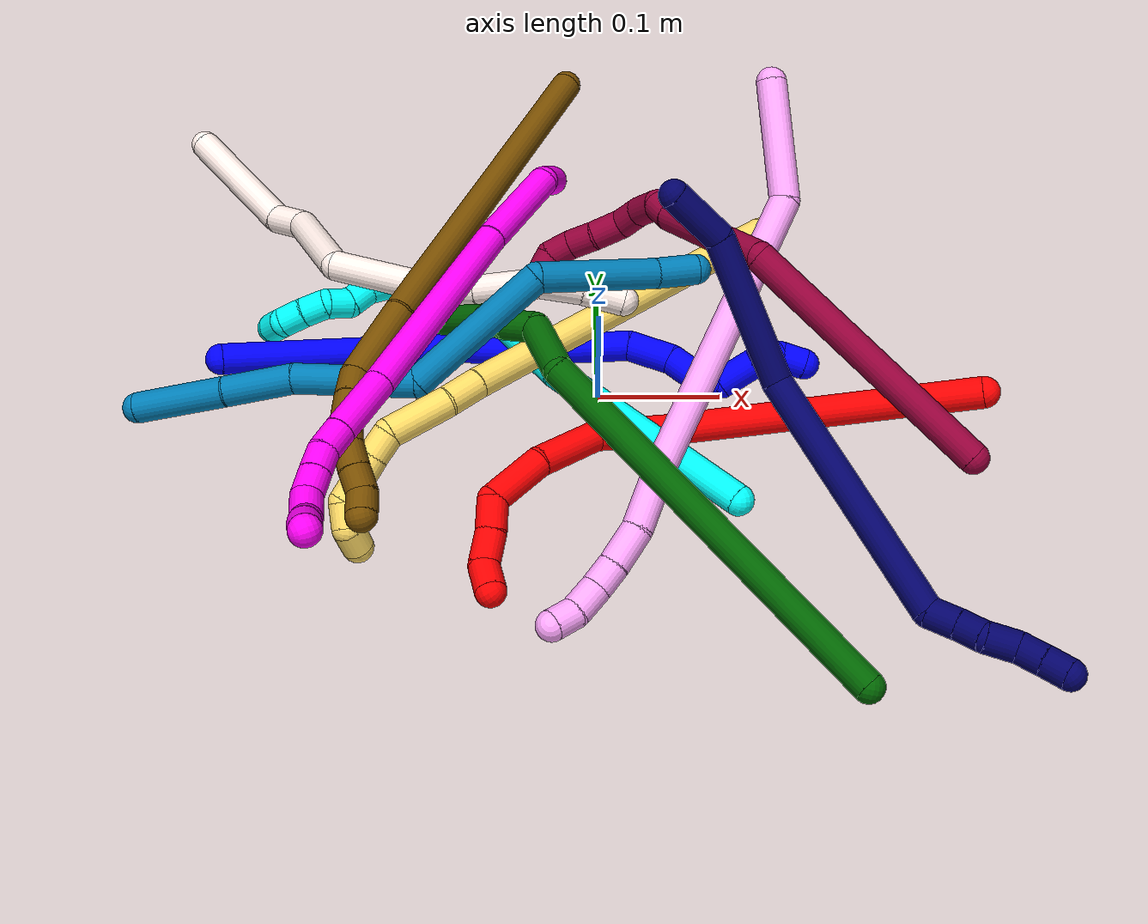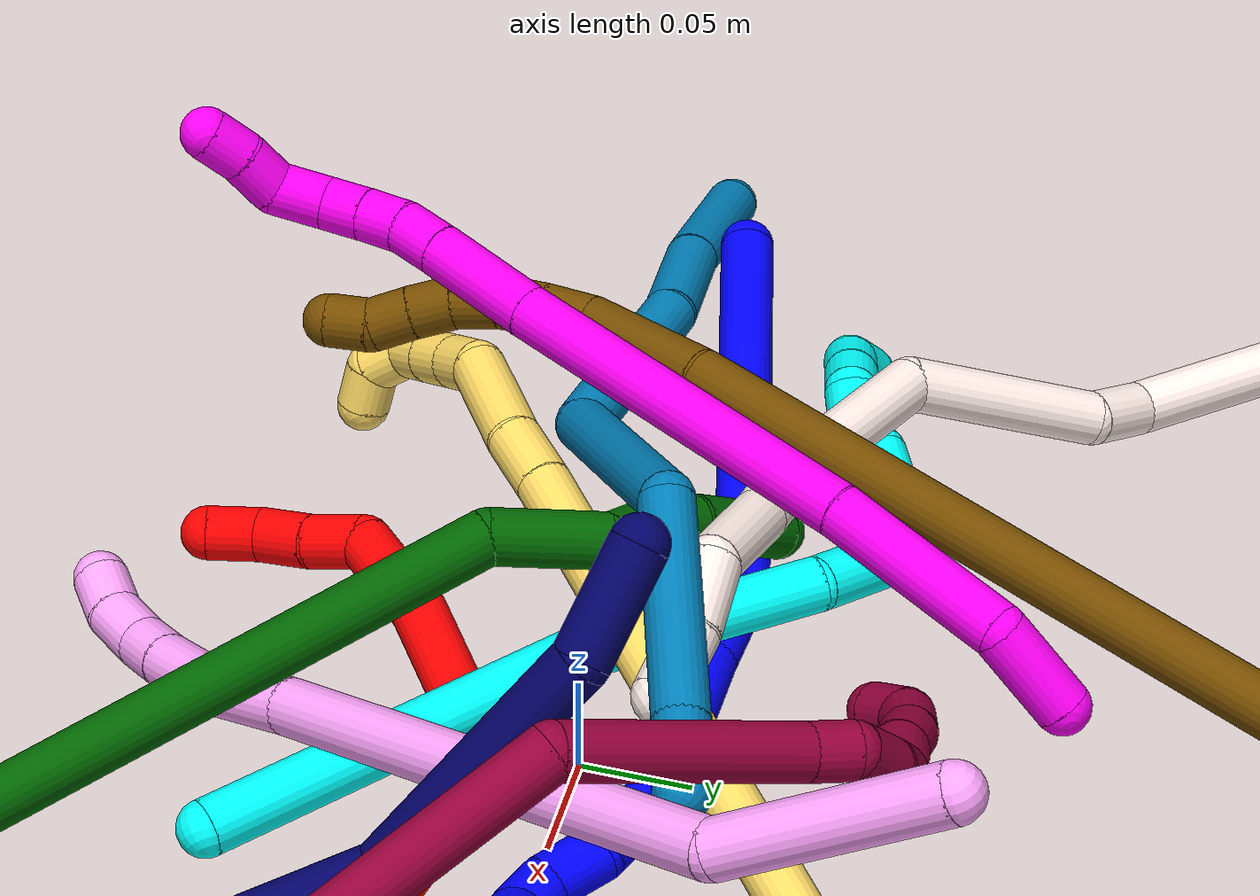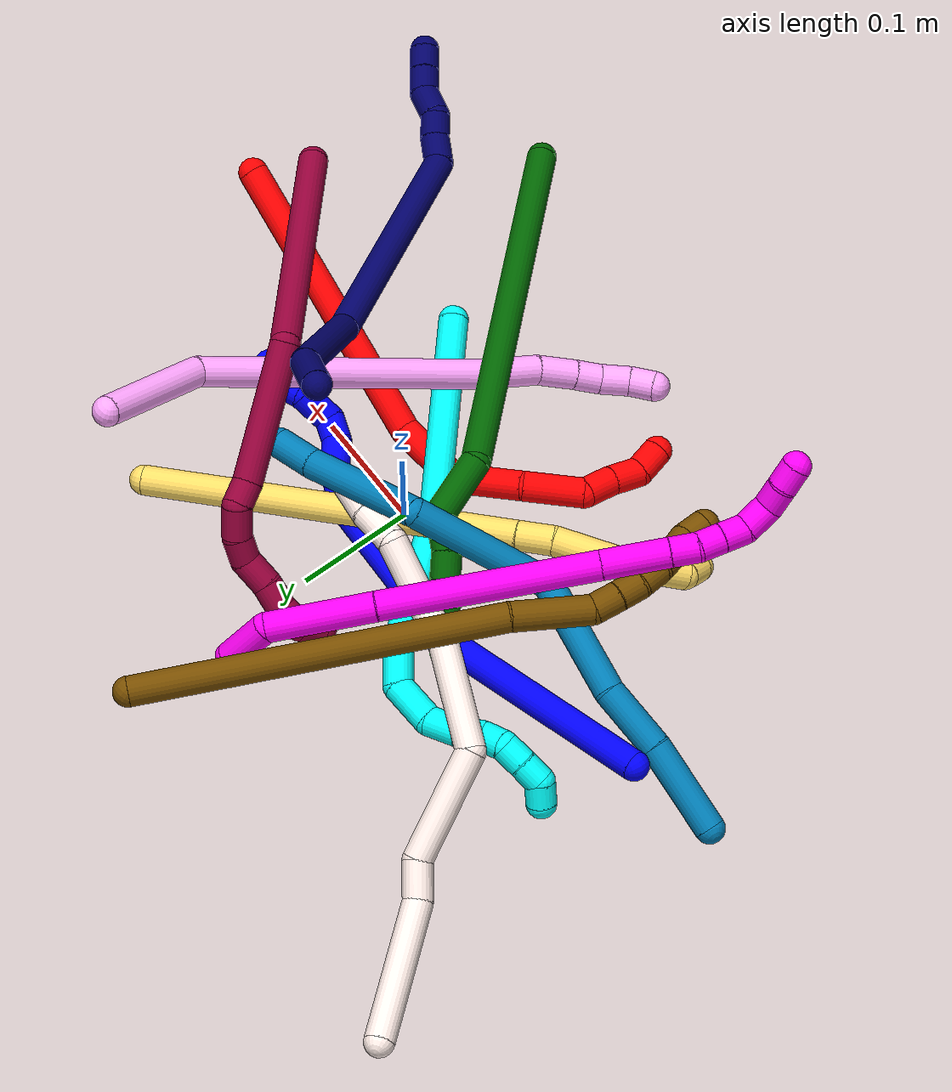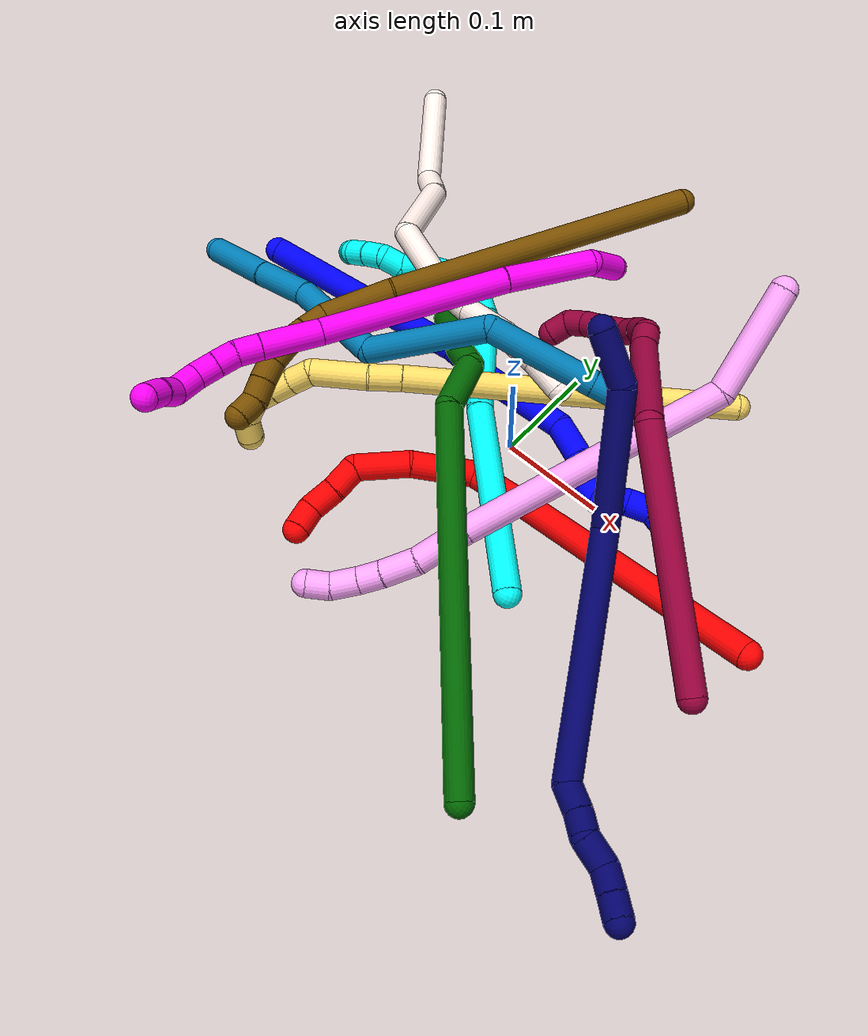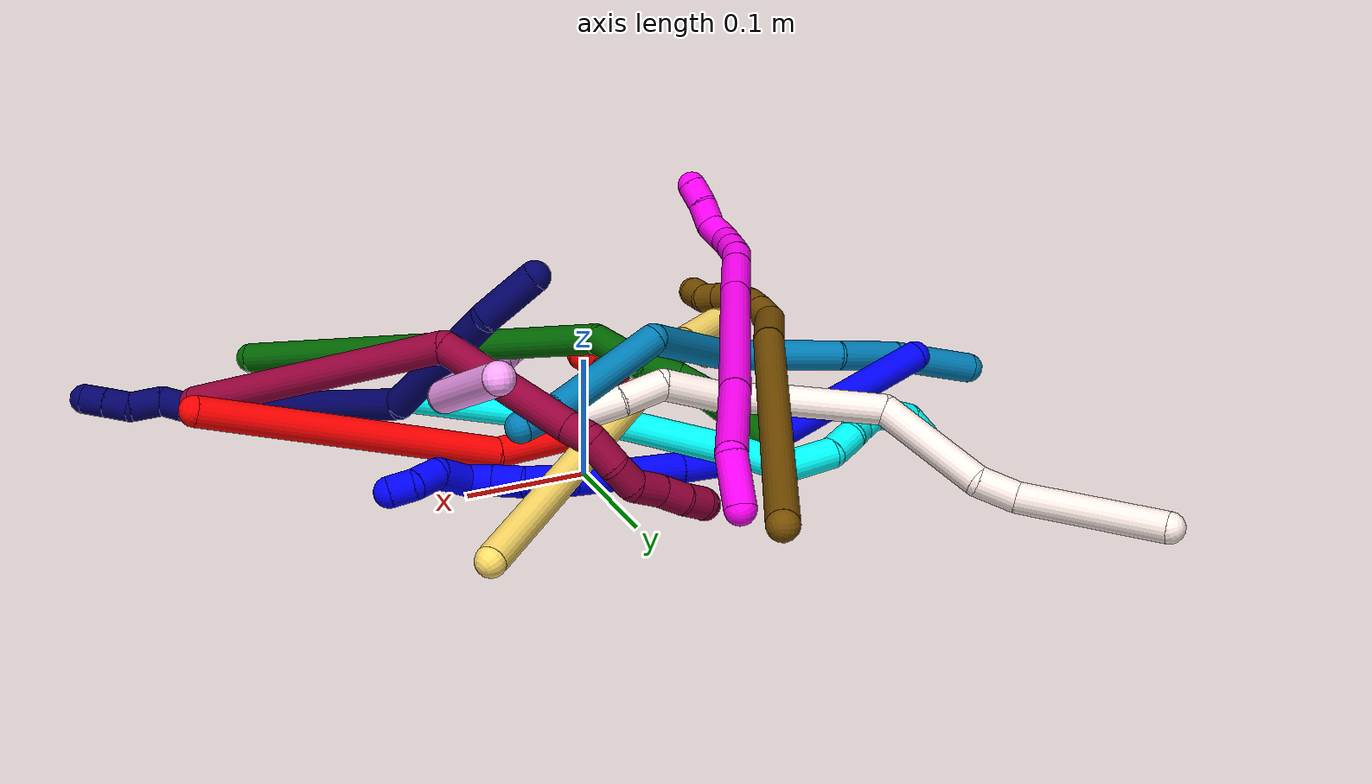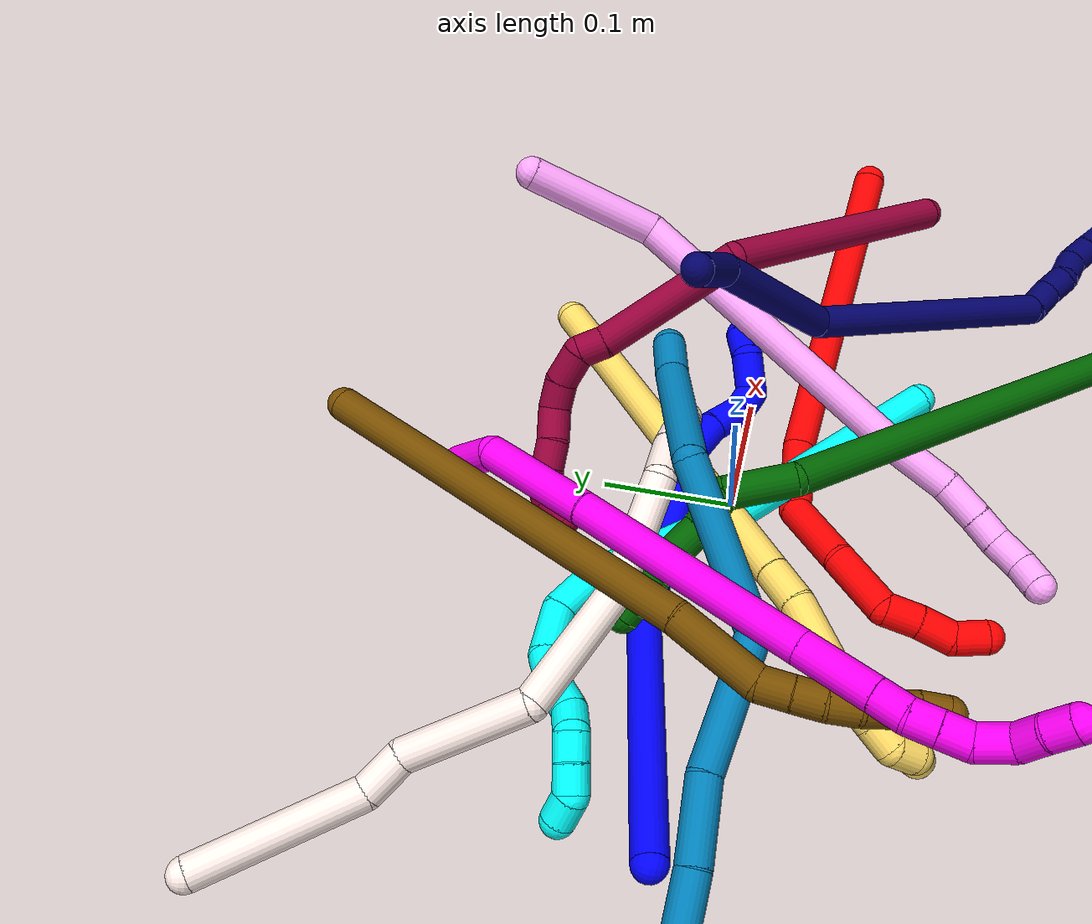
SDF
<sdf version="1.7">
 <world name="default">
  <plugin name="TubeGeneratorPlugin" filename="libtube_generator_plugin.so"/>
  <model name="photoneo_s_sensor">
   <static>1</static>
   <pose>0 0 2 1.57079 1.57079 3.14159</pose>
   <link name="link">
    <inertial><mass>0.1</mass></inertial>
    <sensor name="sensor" type="depth">
     <update_rate>30</update_rate>
     <camera>
      <horizontal_fov>1.22</horizontal_fov>
      <image><width>1920</width><height>1200</height><format>B8G8R8</format></image>
      <clip><near>0.1</near><far>4</far></clip>
      <depth_camera><output>points</output></depth_camera>
     </camera>
     <plugin name="camera_plugin" filename="libgazebo_ros_depth_camera.so">
      <baseline>0.2</baseline>
      <alwaysOn>1</alwaysOn>
      <updateRate>0.0</updateRate>
      <cameraName>camera_ir</cameraName>
      <imageTopicName>/camera/color/image_raw</imageTopicName>
      <cameraInfoTopicName>/camera/color/camera_info</cameraInfoTopicName>
      <depthImageTopicName>/camera/depth/image_raw</depthImageTopicName>
      <depthImageCameraInfoTopicName>/camera/depth/camera_info</depthImageCameraInfoTopicName>
      <pointCloudTopicName>/camera/depth/points</pointCloudTopicName>
      <frameName>fr_optical</frameName>
      <pointCloudCutoff>0.1</pointCloudCutoff>
      <pointCloudCutoffMax>2.0</pointCloudCutoffMax>
      <distortionK1>0</distortionK1>
      <distortionK2>0</distortionK2>
      <distortionK3>0</distortionK3>
      <distortionT1>0</distortionT1>
      <distortionT2>0</distortionT2>
      <CxPrime>0</CxPrime>
      <Cx>0</Cx>
      <Cy>0</Cy>
      <focalLength>0</focalLength>
      <hackBaseline>0</hackBaseline>
     </plugin>
    </sensor>
   </link>
  </model>
  <gravity>0 0 -9.8</gravity>
  <magnetic_field>6e-06 2.3e-05 -4.2e-05</magnetic_field>
  <atmosphere type="adiabatic"/>
  <physics name="default_physics" default="0" type="ode">
   <max_step_size>0.003</max_step_size>
   <real_time_factor>1</real_time_factor>
   <real_time_update_rate>1000</real_time_update_rate>
   <max_contacts>10000</max_contacts>
   <ode>
    <solver>
     <type>quick</type>
     <iters>100</iters>
     <sor>1.3</sor>
     <use_dynamic_moi_rescaling>0</use_dynamic_moi_rescaling>
    </solver>
    <constraints>
     <contact_max_correcting_vel>0</contact_max_correcting_vel>
     <contact_surface_layer>0.001</contact_surface_layer>
     <cfm>0</cfm>
     <erp>0.2</erp>
    </constraints>
   </ode>
  </physics>
  <scene><ambient>0.4 0.4 0.4 1</ambient><background>0.7 0.7 0.7 1</background><shadows>0</shadows></scene>
  <audio><device>default</device></audio>
  <spherical_coordinates>
   <surface_model>EARTH_WGS84</surface_model>
   <latitude_deg>0</latitude_deg>
   <longitude_deg>0</longitude_deg>
   <elevation>0</elevation>
   <heading_deg>0</heading_deg>
  </spherical_coordinates>
  <model name="bin">
   <static>1</static>
   <link name="bottom">
    <collision name="collision-bottom">
     <pose>0 0 -0.01 0 -0 0</pose>
     <geometry><box><size>0.8 0.6 0.02</size></box></geometry>
     <surface>
      <friction><ode><mu>100</mu><mu2>100</mu2></ode></friction>
      <contact><collide_bitmask>65535</collide_bitmask></contact>
     </surface>
    </collision>
   </link>
   <link name="west_wall">
    <collision name="collision-west_wall">
     <pose>-0.41 0 0.1 0 -0 0</pose>
     <geometry><box><size>0.02 0.6 0.2</size></box></geometry>
     <surface>
      <friction><ode><mu>100</mu><mu2>100</mu2></ode></friction>
      <contact><collide_bitmask>65535</collide_bitmask></contact>
     </surface>
    </collision>
   </link>
   <link name="east_wall">
    <collision name="collision-east_wall">
     <pose>0.41 0 0.1 0 -0 0</pose>
     <geometry><box><size>0.02 0.6 0.2</size></box></geometry>
     <surface>
      <friction><ode><mu>100</mu><mu2>100</mu2></ode></friction>
      <contact><collide_bitmask>65535</collide_bitmask></contact>
     </surface>
    </collision>
   </link>
   <link name="south_wall">
    <collision name="collision-south_wall">
     <pose>0 -0.31 0.1 0 -0 0</pose>
     <geometry><box><size>0.8 0.02 0.2</size></box></geometry>
     <surface>
      <friction><ode><mu>100</mu><mu2>100</mu2></ode></friction>
      <contact><collide_bitmask>65535</collide_bitmask></contact>
     </surface>
    </collision>
   </link>
   <link name="north_wall">
    <collision name="collision-north_wall">
     <pose>0 0.31 0.1 0 -0 0</pose>
     <geometry><box><size>0.8 0.02 0.2</size></box></geometry>
     <surface>
      <friction><ode><mu>100</mu><mu2>100</mu2></ode></friction>
      <contact><collide_bitmask>65535</collide_bitmask></contact>
     </surface>
    </collision>
   </link>
  </model>
  <model name="1">
   <static>0</static>
   <link name="1">
    <collision name="collision-cylinder-e_1_1_4">
     <pose>0.096106 0.019782 0.01966 -0.788488 1.28836 -0.605694</pose>
     <geometry><cylinder><radius>0.0125</radius><length>0.200142</length></cylinder></geometry>
     <surface>
      <friction><ode><mu>1.16</mu><mu2>1.16</mu2><slip1>0</slip1><slip2>0</slip2></ode></friction>
      <contact><ode><kp>1e+06</kp><kd>1</kd><max_vel>0</max_vel><min_depth>0.001</min_depth></ode></contact>
     </surface>
    </collision>
    <visual name="visual-cylinder-e_1_1_4">
     <pose>0.096106 0.019782 0.01966 -0.788488 1.28836 -0.605694</pose>
     <geometry><cylinder><radius>0.0125</radius><length>0.200142</length></cylinder></geometry>
     <material><ambient>0 0 1 1</ambient></material>
    </visual>
    <collision name="collision-cylinder-e_2_4_5">
     <pose>0.215535 0.038448 0.037711 2.53529 1.48702 2.48583</pose>
     <geometry><cylinder><radius>0.0125</radius><length>0.04681</length></cylinder></geometry>
     <surface>
      <friction><ode><mu>1.16</mu><mu2>1.16</mu2><slip1>0</slip1><slip2>0</slip2></ode></friction>
      <contact><ode><kp>1e+06</kp><kd>1</kd><max_vel>0</max_vel><min_depth>0.001</min_depth></ode></contact>
     </surface>
    </collision>
    <visual name="visual-cylinder-e_2_4_5">
     <pose>0.215535 0.038448 0.037711 2.53529 1.48702 2.48583</pose>
     <geometry><cylinder><radius>0.0125</radius><length>0.04681</length></cylinder></geometry>
     <material><ambient>0 0 1 1</ambient></material>
    </visual>
    <collision name="collision-cylinder-e_3_5_6">
     <pose>0.284691 0.032471 0.036363 1.51694 1.46499 1.41158</pose>
     <geometry><cylinder><radius>0.0125</radius><length>0.092182</length></cylinder></geometry>
     <surface>
      <friction><ode><mu>1.16</mu><mu2>1.16</mu2><slip1>0</slip1><slip2>0</slip2></ode></friction>
      <contact><ode><kp>1e+06</kp><kd>1</kd><max_vel>0</max_vel><min_depth>0.001</min_depth></ode></contact>
     </surface>
    </collision>
    <visual name="visual-cylinder-e_3_5_6">
     <pose>0.284691 0.032471 0.036363 1.51694 1.46499 1.41158</pose>
     <geometry><cylinder><radius>0.0125</radius><length>0.092182</length></cylinder></geometry>
     <material><ambient>0 0 1 1</ambient></material>
    </visual>
    <collision name="collision-cylinder-e_4_6_7">
     <pose>0.347883 0.026488 0.029603 2.98312 1.18197 2.90602</pose>
     <geometry><cylinder><radius>0.0125</radius><length>0.037518</length></cylinder></geometry>
     <surface>
      <friction><ode><mu>1.16</mu><mu2>1.16</mu2><slip1>0</slip1><slip2>0</slip2></ode></friction>
      <contact><ode><kp>1e+06</kp><kd>1</kd><max_vel>0</max_vel><min_depth>0.001</min_depth></ode></contact>
     </surface>
    </collision>
    <visual name="visual-cylinder-e_4_6_7">
     <pose>0.347883 0.026488 0.029603 2.98312 1.18197 2.90602</pose>
     <geometry><cylinder><radius>0.0125</radius><length>0.037518</length></cylinder></geometry>
     <material><ambient>0 0 1 1</ambient></material>
    </visual>
    <collision name="collision-cylinder-e_5_7_8">
     <pose>0.37542 0.024804 0.013856 3.0773 0.861122 3.00179</pose>
     <geometry><cylinder><radius>0.0125</radius><length>0.026834</length></cylinder></geometry>
     <surface>
      <friction><ode><mu>1.16</mu><mu2>1.16</mu2><slip1>0</slip1><slip2>0</slip2></ode></friction>
      <contact><ode><kp>1e+06</kp><kd>1</kd><max_vel>0</max_vel><min_depth>0.001</min_depth></ode></contact>
     </surface>
    </collision>
    <visual name="visual-cylinder-e_5_7_8">
     <pose>0.37542 0.024804 0.013856 3.0773 0.861122 3.00179</pose>
     <geometry><cylinder><radius>0.0125</radius><length>0.026834</length></cylinder></geometry>
     <material><ambient>0 0 1 1</ambient></material>
    </visual>
    <collision name="collision-cylinder-e_6_8_9">
     <pose>0.395554 0.022967 0.001731 2.78263 1.22099 2.63414</pose>
     <geometry><cylinder><radius>0.0125</radius><length>0.021196</length></cylinder></geometry>
     <surface>
      <friction><ode><mu>1.16</mu><mu2>1.16</mu2><slip1>0</slip1><slip2>0</slip2></ode></friction>
      <contact><ode><kp>1e+06</kp><kd>1</kd><max_vel>0</max_vel><min_depth>0.001</min_depth></ode></contact>
     </surface>
    </collision>
    <visual name="visual-cylinder-e_6_8_9">
     <pose>0.395554 0.022967 0.001731 2.78263 1.22099 2.63414</pose>
     <geometry><cylinder><radius>0.0125</radius><length>0.021196</length></cylinder></geometry>
     <material><ambient>0 0 1 1</ambient></material>
    </visual>
    <collision name="collision-cylinder-e_7_9_10">
     <pose>0.41833 0.014453 0.003796 0.924021 0.955072 0.504394</pose>
     <geometry><cylinder><radius>0.0125</radius><length>0.031408</length></cylinder></geometry>
     <surface>
      <friction><ode><mu>1.16</mu><mu2>1.16</mu2><slip1>0</slip1><slip2>0</slip2></ode></friction>
      <contact><ode><kp>1e+06</kp><kd>1</kd><max_vel>0</max_vel><min_depth>0.001</min_depth></ode></contact>
     </surface>
    </collision>
    <visual name="visual-cylinder-e_7_9_10">
     <pose>0.41833 0.014453 0.003796 0.924021 0.955072 0.504394</pose>
     <geometry><cylinder><radius>0.0125</radius><length>0.031408</length></cylinder></geometry>
     <material><ambient>0 0 1 1</ambient></material>
    </visual>
    <collision name="collision-cylinder-e_8_10_11">
     <pose>0.442259 0.00829 0.013271 -0.262026 1.21324 -0.18236</pose>
     <geometry><cylinder><radius>0.0125</radius><length>0.023718</length></cylinder></geometry>
     <surface>
      <friction><ode><mu>1.16</mu><mu2>1.16</mu2><slip1>0</slip1><slip2>0</slip2></ode></friction>
      <contact><ode><kp>1e+06</kp><kd>1</kd><max_vel>0</max_vel><min_depth>0.001</min_depth></ode></contact>
     </surface>
    </collision>
    <visual name="visual-cylinder-e_8_10_11">
     <pose>0.442259 0.00829 0.013271 -0.262026 1.21324 -0.18236</pose>
     <geometry><cylinder><radius>0.0125</radius><length>0.023718</length></cylinder></geometry>
     <material><ambient>0 0 1 1</ambient></material>
    </visual>
    <collision name="collision-cylinder-e_9_11_2">
     <pose>0.46304 0.010982 0.014878 -2.54902 1.27993 -2.36333</pose>
     <geometry><cylinder><radius>0.0125</radius><length>0.020191</length></cylinder></geometry>
     <surface>
      <friction><ode><mu>1.16</mu><mu2>1.16</mu2><slip1>0</slip1><slip2>0</slip2></ode></friction>
      <contact><ode><kp>1e+06</kp><kd>1</kd><max_vel>0</max_vel><min_depth>0.001</min_depth></ode></contact>
     </surface>
    </collision>
    <visual name="visual-cylinder-e_9_11_2">
     <pose>0.46304 0.010982 0.014878 -2.54902 1.27993 -2.36333</pose>
     <geometry><cylinder><radius>0.0125</radius><length>0.020191</length></cylinder></geometry>
     <material><ambient>0 0 1 1</ambient></material>
    </visual>
    <collision name="collision-sphere-2">
     <pose>0.472712 0.012599 0.012476 0 -0 0</pose>
     <geometry><sphere><radius>0.0125</radius></sphere></geometry>
     <surface>
      <friction><ode><mu>1.16</mu><mu2>1.16</mu2><slip1>0</slip1><slip2>0</slip2></ode></friction>
      <contact><ode><kp>1e+06</kp><kd>1</kd><max_vel>0</max_vel><min_depth>0.001</min_depth></ode></contact>
     </surface>
    </collision>
    <visual name="visual-sphere-2">
     <pose>0.472712 0.012599 0.012476 0 -0 0</pose>
     <geometry><sphere><radius>0.0125</radius></sphere></geometry>
     <material><ambient>0 0 1 1</ambient></material>
    </visual>
    <collision name="collision-sphere-11">
     <pose>0.453368 0.009365 0.01728 0 -0 0</pose>
     <geometry><sphere><radius>0.0125</radius></sphere></geometry>
     <surface>
      <friction><ode><mu>1.16</mu><mu2>1.16</mu2><slip1>0</slip1><slip2>0</slip2></ode></friction>
      <contact><ode><kp>1e+06</kp><kd>1</kd><max_vel>0</max_vel><min_depth>0.001</min_depth></ode></contact>
     </surface>
    </collision>
    <visual name="visual-sphere-11">
     <pose>0.453368 0.009365 0.01728 0 -0 0</pose>
     <geometry><sphere><radius>0.0125</radius></sphere></geometry>
     <material><ambient>0 0 1 1</ambient></material>
    </visual>
    <collision name="collision-sphere-10">
     <pose>0.43115 0.007214 0.009262 0 -0 0</pose>
     <geometry><sphere><radius>0.0125</radius></sphere></geometry>
     <surface>
      <friction><ode><mu>1.16</mu><mu2>1.16</mu2><slip1>0</slip1><slip2>0</slip2></ode></friction>
      <contact><ode><kp>1e+06</kp><kd>1</kd><max_vel>0</max_vel><min_depth>0.001</min_depth></ode></contact>
     </surface>
    </collision>
    <visual name="visual-sphere-10">
     <pose>0.43115 0.007214 0.009262 0 -0 0</pose>
     <geometry><sphere><radius>0.0125</radius></sphere></geometry>
     <material><ambient>0 0 1 1</ambient></material>
    </visual>
    <collision name="collision-sphere-9">
     <pose>0.40551 0.021691 -0.001669 0 -0 0</pose>
     <geometry><sphere><radius>0.0125</radius></sphere></geometry>
     <surface>
      <friction><ode><mu>1.16</mu><mu2>1.16</mu2><slip1>0</slip1><slip2>0</slip2></ode></friction>
      <contact><ode><kp>1e+06</kp><kd>1</kd><max_vel>0</max_vel><min_depth>0.001</min_depth></ode></contact>
     </surface>
    </collision>
    <visual name="visual-sphere-9">
     <pose>0.40551 0.021691 -0.001669 0 -0 0</pose>
     <geometry><sphere><radius>0.0125</radius></sphere></geometry>
     <material><ambient>0 0 1 1</ambient></material>
    </visual>
    <collision name="collision-sphere-4">
     <pose>0.192212 0.039564 0.03932 0 -0 0</pose>
     <geometry><sphere><radius>0.0125</radius></sphere></geometry>
     <surface>
      <friction><ode><mu>1.16</mu><mu2>1.16</mu2><slip1>0</slip1><slip2>0</slip2></ode></friction>
      <contact><ode><kp>1e+06</kp><kd>1</kd><max_vel>0</max_vel><min_depth>0.001</min_depth></ode></contact>
     </surface>
    </collision>
    <visual name="visual-sphere-4">
     <pose>0.192212 0.039564 0.03932 0 -0 0</pose>
     <geometry><sphere><radius>0.0125</radius></sphere></geometry>
     <material><ambient>0 0 1 1</ambient></material>
    </visual>
    <collision name="collision-sphere-1">
     <geometry><sphere><radius>0.0125</radius></sphere></geometry>
     <surface>
      <friction><ode><mu>1.16</mu><mu2>1.16</mu2><slip1>0</slip1><slip2>0</slip2></ode></friction>
      <contact><ode><kp>1e+06</kp><kd>1</kd><max_vel>0</max_vel><min_depth>0.001</min_depth></ode></contact>
     </surface>
    </collision>
    <visual name="visual-sphere-1">
     <geometry><sphere><radius>0.0125</radius></sphere></geometry>
     <material><ambient>0 0 1 1</ambient></material>
    </visual>
    <collision name="collision-sphere-8">
     <pose>0.385597 0.024243 0.005132 0 -0 0</pose>
     <geometry><sphere><radius>0.0125</radius></sphere></geometry>
     <surface>
      <friction><ode><mu>1.16</mu><mu2>1.16</mu2><slip1>0</slip1><slip2>0</slip2></ode></friction>
      <contact><ode><kp>1e+06</kp><kd>1</kd><max_vel>0</max_vel><min_depth>0.001</min_depth></ode></contact>
     </surface>
    </collision>
    <visual name="visual-sphere-8">
     <pose>0.385597 0.024243 0.005132 0 -0 0</pose>
     <geometry><sphere><radius>0.0125</radius></sphere></geometry>
     <material><ambient>0 0 1 1</ambient></material>
    </visual>
    <collision name="collision-sphere-5">
     <pose>0.238858 0.037332 0.036101 0 -0 0</pose>
     <geometry><sphere><radius>0.0125</radius></sphere></geometry>
     <surface>
      <friction><ode><mu>1.16</mu><mu2>1.16</mu2><slip1>0</slip1><slip2>0</slip2></ode></friction>
      <contact><ode><kp>1e+06</kp><kd>1</kd><max_vel>0</max_vel><min_depth>0.001</min_depth></ode></contact>
     </surface>
    </collision>
    <visual name="visual-sphere-5">
     <pose>0.238858 0.037332 0.036101 0 -0 0</pose>
     <geometry><sphere><radius>0.0125</radius></sphere></geometry>
     <material><ambient>0 0 1 1</ambient></material>
    </visual>
    <collision name="collision-sphere-6">
     <pose>0.330524 0.027611 0.036625 0 -0 0</pose>
     <geometry><sphere><radius>0.0125</radius></sphere></geometry>
     <surface>
      <friction><ode><mu>1.16</mu><mu2>1.16</mu2><slip1>0</slip1><slip2>0</slip2></ode></friction>
      <contact><ode><kp>1e+06</kp><kd>1</kd><max_vel>0</max_vel><min_depth>0.001</min_depth></ode></contact>
     </surface>
    </collision>
    <visual name="visual-sphere-6">
     <pose>0.330524 0.027611 0.036625 0 -0 0</pose>
     <geometry><sphere><radius>0.0125</radius></sphere></geometry>
     <material><ambient>0 0 1 1</ambient></material>
    </visual>
    <collision name="collision-sphere-7">
     <pose>0.365242 0.025366 0.02258 0 -0 0</pose>
     <geometry><sphere><radius>0.0125</radius></sphere></geometry>
     <surface>
      <friction><ode><mu>1.16</mu><mu2>1.16</mu2><slip1>0</slip1><slip2>0</slip2></ode></friction>
      <contact><ode><kp>1e+06</kp><kd>1</kd><max_vel>0</max_vel><min_depth>0.001</min_depth></ode></contact>
     </surface>
    </collision>
    <visual name="visual-sphere-7">
     <pose>0.365242 0.025366 0.02258 0 -0 0</pose>
     <geometry><sphere><radius>0.0125</radius></sphere></geometry>
     <material><ambient>0 0 1 1</ambient></material>
    </visual>
    <inertial>
     <pose>0.240111 0.023541 0.022611 0 -0 0</pose>
     <mass>0.5</mass>
     <inertia>
      <ixx>9.2e-05</ixx>
      <ixy>0</ixy>
      <ixz>0</ixz>
      <iyy>0.000652</iyy>
      <iyz>0</iyz>
      <izz>-0.000866</izz>
     </inertia>
    </inertial>
   </link>
   <pose>-0.3033 -0.001185 0.051091 -1.4149 0.034552 0.002685</pose>
  </model>
  <model name="2">
   <static>0</static>
   <link name="2">
    <collision name="collision-cylinder-e_1_1_4">
     <pose>0.016493 -0.044263 0.115802 0.365093 0.132257 0.024449</pose>
     <geometry><cylinder><radius>0.0125</radius><length>0.250131</length></cylinder></geometry>
     <surface>
      <friction><ode><mu>1.16</mu><mu2>1.16</mu2><slip1>0</slip1><slip2>0</slip2></ode></friction>
      <contact><ode><kp>1e+06</kp><kd>1</kd><max_vel>0</max_vel><min_depth>0.001</min_depth></ode></contact>
     </surface>
    </collision>
    <visual name="visual-cylinder-e_1_1_4">
     <pose>0.016493 -0.044263 0.115802 0.365093 0.132257 0.024449</pose>
     <geometry><cylinder><radius>0.0125</radius><length>0.250131</length></cylinder></geometry>
     <material><ambient>1 0 0 1</ambient></material>
    </visual>
    <collision name="collision-cylinder-e_2_4_5">
     <pose>0.030352 -0.10603 0.255807 0.626139 -0.087922 -0.028478</pose>
     <geometry><cylinder><radius>0.0125</radius><length>0.05997</length></cylinder></geometry>
     <surface>
      <friction><ode><mu>1.16</mu><mu2>1.16</mu2><slip1>0</slip1><slip2>0</slip2></ode></friction>
      <contact><ode><kp>1e+06</kp><kd>1</kd><max_vel>0</max_vel><min_depth>0.001</min_depth></ode></contact>
     </surface>
    </collision>
    <visual name="visual-cylinder-e_2_4_5">
     <pose>0.030352 -0.10603 0.255807 0.626139 -0.087922 -0.028478</pose>
     <geometry><cylinder><radius>0.0125</radius><length>0.05997</length></cylinder></geometry>
     <material><ambient>1 0 0 1</ambient></material>
    </visual>
    <collision name="collision-cylinder-e_3_5_6">
     <pose>0.008494 -0.140638 0.295798 0.825411 -0.690343 -0.31231</pose>
     <geometry><cylinder><radius>0.0125</radius><length>0.060379</length></cylinder></geometry>
     <surface>
      <friction><ode><mu>1.16</mu><mu2>1.16</mu2><slip1>0</slip1><slip2>0</slip2></ode></friction>
      <contact><ode><kp>1e+06</kp><kd>1</kd><max_vel>0</max_vel><min_depth>0.001</min_depth></ode></contact>
     </surface>
    </collision>
    <visual name="visual-cylinder-e_3_5_6">
     <pose>0.008494 -0.140638 0.295798 0.825411 -0.690343 -0.31231</pose>
     <geometry><cylinder><radius>0.0125</radius><length>0.060379</length></cylinder></geometry>
     <material><ambient>1 0 0 1</ambient></material>
    </visual>
    <collision name="collision-cylinder-e_4_6_7">
     <pose>-0.028611 -0.166282 0.327426 0.494446 -0.782189 -0.207388</pose>
     <geometry><cylinder><radius>0.0125</radius><length>0.050737</length></cylinder></geometry>
     <surface>
      <friction><ode><mu>1.16</mu><mu2>1.16</mu2><slip1>0</slip1><slip2>0</slip2></ode></friction>
      <contact><ode><kp>1e+06</kp><kd>1</kd><max_vel>0</max_vel><min_depth>0.001</min_depth></ode></contact>
     </surface>
    </collision>
    <visual name="visual-cylinder-e_4_6_7">
     <pose>-0.028611 -0.166282 0.327426 0.494446 -0.782189 -0.207388</pose>
     <geometry><cylinder><radius>0.0125</radius><length>0.050737</length></cylinder></geometry>
     <material><ambient>1 0 0 1</ambient></material>
    </visual>
    <collision name="collision-cylinder-e_5_7_8">
     <pose>-0.058797 -0.170743 0.347125 -0.813206 -1.1427 0.540116</pose>
     <geometry><cylinder><radius>0.0125</radius><length>0.027053</length></cylinder></geometry>
     <surface>
      <friction><ode><mu>1.16</mu><mu2>1.16</mu2><slip1>0</slip1><slip2>0</slip2></ode></friction>
      <contact><ode><kp>1e+06</kp><kd>1</kd><max_vel>0</max_vel><min_depth>0.001</min_depth></ode></contact>
     </surface>
    </collision>
    <visual name="visual-cylinder-e_5_7_8">
     <pose>-0.058797 -0.170743 0.347125 -0.813206 -1.1427 0.540116</pose>
     <geometry><cylinder><radius>0.0125</radius><length>0.027053</length></cylinder></geometry>
     <material><ambient>1 0 0 1</ambient></material>
    </visual>
    <collision name="collision-cylinder-e_6_8_9">
     <pose>-0.083371 -0.164039 0.356232 -0.463587 -1.12462 0.295323</pose>
     <geometry><cylinder><radius>0.0125</radius><length>0.027199</length></cylinder></geometry>
     <surface>
      <friction><ode><mu>1.16</mu><mu2>1.16</mu2><slip1>0</slip1><slip2>0</slip2></ode></friction>
      <contact><ode><kp>1e+06</kp><kd>1</kd><max_vel>0</max_vel><min_depth>0.001</min_depth></ode></contact>
     </surface>
    </collision>
    <visual name="visual-cylinder-e_6_8_9">
     <pose>-0.083371 -0.164039 0.356232 -0.463587 -1.12462 0.295323</pose>
     <geometry><cylinder><radius>0.0125</radius><length>0.027199</length></cylinder></geometry>
     <material><ambient>1 0 0 1</ambient></material>
    </visual>
    <collision name="collision-cylinder-e_7_9_2">
     <pose>-0.107475 -0.158493 0.360128 -2.00442 -1.30513 1.74889</pose>
     <geometry><cylinder><radius>0.0125</radius><length>0.024532</length></cylinder></geometry>
     <surface>
      <friction><ode><mu>1.16</mu><mu2>1.16</mu2><slip1>0</slip1><slip2>0</slip2></ode></friction>
      <contact><ode><kp>1e+06</kp><kd>1</kd><max_vel>0</max_vel><min_depth>0.001</min_depth></ode></contact>
     </surface>
    </collision>
    <visual name="visual-cylinder-e_7_9_2">
     <pose>-0.107475 -0.158493 0.360128 -2.00442 -1.30513 1.74889</pose>
     <geometry><cylinder><radius>0.0125</radius><length>0.024532</length></cylinder></geometry>
     <material><ambient>1 0 0 1</ambient></material>
    </visual>
    <collision name="collision-sphere-2">
     <pose>-0.11931 -0.15557 0.358775 0 -0 0</pose>
     <geometry><sphere><radius>0.0125</radius></sphere></geometry>
     <surface>
      <friction><ode><mu>1.16</mu><mu2>1.16</mu2><slip1>0</slip1><slip2>0</slip2></ode></friction>
      <contact><ode><kp>1e+06</kp><kd>1</kd><max_vel>0</max_vel><min_depth>0.001</min_depth></ode></contact>
     </surface>
    </collision>
    <visual name="visual-sphere-2">
     <pose>-0.11931 -0.15557 0.358775 0 -0 0</pose>
     <geometry><sphere><radius>0.0125</radius></sphere></geometry>
     <material><ambient>1 0 0 1</ambient></material>
    </visual>
    <collision name="collision-sphere-9">
     <pose>-0.095639 -0.161415 0.361481 0 -0 0</pose>
     <geometry><sphere><radius>0.0125</radius></sphere></geometry>
     <surface>
      <friction><ode><mu>1.16</mu><mu2>1.16</mu2><slip1>0</slip1><slip2>0</slip2></ode></friction>
      <contact><ode><kp>1e+06</kp><kd>1</kd><max_vel>0</max_vel><min_depth>0.001</min_depth></ode></contact>
     </surface>
    </collision>
    <visual name="visual-sphere-9">
     <pose>-0.095639 -0.161415 0.361481 0 -0 0</pose>
     <geometry><sphere><radius>0.0125</radius></sphere></geometry>
     <material><ambient>1 0 0 1</ambient></material>
    </visual>
    <collision name="collision-sphere-4">
     <pose>0.032985 -0.088526 0.231604 0 -0 0</pose>
     <geometry><sphere><radius>0.0125</radius></sphere></geometry>
     <surface>
      <friction><ode><mu>1.16</mu><mu2>1.16</mu2><slip1>0</slip1><slip2>0</slip2></ode></friction>
      <contact><ode><kp>1e+06</kp><kd>1</kd><max_vel>0</max_vel><min_depth>0.001</min_depth></ode></contact>
     </surface>
    </collision>
    <visual name="visual-sphere-4">
     <pose>0.032985 -0.088526 0.231604 0 -0 0</pose>
     <geometry><sphere><radius>0.0125</radius></sphere></geometry>
     <material><ambient>1 0 0 1</ambient></material>
    </visual>
    <collision name="collision-sphere-1">
     <geometry><sphere><radius>0.0125</radius></sphere></geometry>
     <surface>
      <friction><ode><mu>1.16</mu><mu2>1.16</mu2><slip1>0</slip1><slip2>0</slip2></ode></friction>
      <contact><ode><kp>1e+06</kp><kd>1</kd><max_vel>0</max_vel><min_depth>0.001</min_depth></ode></contact>
     </surface>
    </collision>
    <visual name="visual-sphere-1">
     <geometry><sphere><radius>0.0125</radius></sphere></geometry>
     <material><ambient>1 0 0 1</ambient></material>
    </visual>
    <collision name="collision-sphere-8">
     <pose>-0.071103 -0.166663 0.350983 0 -0 0</pose>
     <geometry><sphere><radius>0.0125</radius></sphere></geometry>
     <surface>
      <friction><ode><mu>1.16</mu><mu2>1.16</mu2><slip1>0</slip1><slip2>0</slip2></ode></friction>
      <contact><ode><kp>1e+06</kp><kd>1</kd><max_vel>0</max_vel><min_depth>0.001</min_depth></ode></contact>
     </surface>
    </collision>
    <visual name="visual-sphere-8">
     <pose>-0.071103 -0.166663 0.350983 0 -0 0</pose>
     <geometry><sphere><radius>0.0125</radius></sphere></geometry>
     <material><ambient>1 0 0 1</ambient></material>
    </visual>
    <collision name="collision-sphere-5">
     <pose>0.027719 -0.123534 0.28001 0 -0 0</pose>
     <geometry><sphere><radius>0.0125</radius></sphere></geometry>
     <surface>
      <friction><ode><mu>1.16</mu><mu2>1.16</mu2><slip1>0</slip1><slip2>0</slip2></ode></friction>
      <contact><ode><kp>1e+06</kp><kd>1</kd><max_vel>0</max_vel><min_depth>0.001</min_depth></ode></contact>
     </surface>
    </collision>
    <visual name="visual-sphere-5">
     <pose>0.027719 -0.123534 0.28001 0 -0 0</pose>
     <geometry><sphere><radius>0.0125</radius></sphere></geometry>
     <material><ambient>1 0 0 1</ambient></material>
    </visual>
    <collision name="collision-sphere-6">
     <pose>-0.01073 -0.157743 0.311585 0 -0 0</pose>
     <geometry><sphere><radius>0.0125</radius></sphere></geometry>
     <surface>
      <friction><ode><mu>1.16</mu><mu2>1.16</mu2><slip1>0</slip1><slip2>0</slip2></ode></friction>
      <contact><ode><kp>1e+06</kp><kd>1</kd><max_vel>0</max_vel><min_depth>0.001</min_depth></ode></contact>
     </surface>
    </collision>
    <visual name="visual-sphere-6">
     <pose>-0.01073 -0.157743 0.311585 0 -0 0</pose>
     <geometry><sphere><radius>0.0125</radius></sphere></geometry>
     <material><ambient>1 0 0 1</ambient></material>
    </visual>
    <collision name="collision-sphere-7">
     <pose>-0.046491 -0.174822 0.343266 0 -0 0</pose>
     <geometry><sphere><radius>0.0125</radius></sphere></geometry>
     <surface>
      <friction><ode><mu>1.16</mu><mu2>1.16</mu2><slip1>0</slip1><slip2>0</slip2></ode></friction>
      <contact><ode><kp>1e+06</kp><kd>1</kd><max_vel>0</max_vel><min_depth>0.001</min_depth></ode></contact>
     </surface>
    </collision>
    <visual name="visual-sphere-7">
     <pose>-0.046491 -0.174822 0.343266 0 -0 0</pose>
     <geometry><sphere><radius>0.0125</radius></sphere></geometry>
     <material><ambient>1 0 0 1</ambient></material>
    </visual>
    <inertial>
     <pose>-0.002976 -0.094654 0.213387 0 -0 0</pose>
     <mass>0.5</mass>
     <inertia>
      <ixx>0.001365</ixx>
      <ixy>0</ixy>
      <ixz>0</ixz>
      <iyy>0.001294</iyy>
      <iyz>0</iyz>
      <izz>0.000377</izz>
     </inertia>
    </inertial>
   </link>
   <pose>0.296525 -0.064399 0.082795 -2.21026 0.146643 1.5792</pose>
  </model>
  <model name="3">
   <static>0</static>
   <link name="3">
    <collision name="collision-cylinder-e_1_1_4">
     <pose>-0.083698 0.038808 -0.019661 -2.03973 -1.09146 1.5591</pose>
     <geometry><cylinder><radius>0.0125</radius><length>0.188658</length></cylinder></geometry>
     <surface>
      <friction><ode><mu>1.16</mu><mu2>1.16</mu2><slip1>0</slip1><slip2>0</slip2></ode></friction>
      <contact><ode><kp>1e+06</kp><kd>1</kd><max_vel>0</max_vel><min_depth>0.001</min_depth></ode></contact>
     </surface>
    </collision>
    <visual name="visual-cylinder-e_1_1_4">
     <pose>-0.083698 0.038808 -0.019661 -2.03973 -1.09146 1.5591</pose>
     <geometry><cylinder><radius>0.0125</radius><length>0.188658</length></cylinder></geometry>
     <material><ambient>0.003922 1 0.996078 1</ambient></material>
    </visual>
    <collision name="collision-cylinder-e_2_4_5">
     <pose>-0.217781 0.097986 -0.041542 -1.67939 -1.18453 1.28723</pose>
     <geometry><cylinder><radius>0.0125</radius><length>0.108785</length></cylinder></geometry>
     <surface>
      <friction><ode><mu>1.16</mu><mu2>1.16</mu2><slip1>0</slip1><slip2>0</slip2></ode></friction>
      <contact><ode><kp>1e+06</kp><kd>1</kd><max_vel>0</max_vel><min_depth>0.001</min_depth></ode></contact>
     </surface>
    </collision>
    <visual name="visual-cylinder-e_2_4_5">
     <pose>-0.217781 0.097986 -0.041542 -1.67939 -1.18453 1.28723</pose>
     <geometry><cylinder><radius>0.0125</radius><length>0.108785</length></cylinder></geometry>
     <material><ambient>0.003922 1 0.996078 1</ambient></material>
    </visual>
    <collision name="collision-cylinder-e_3_5_6">
     <pose>-0.281794 0.129408 -0.047062 -1.86085 -0.868449 1.11342</pose>
     <geometry><cylinder><radius>0.0125</radius><length>0.035707</length></cylinder></geometry>
     <surface>
      <friction><ode><mu>1.16</mu><mu2>1.16</mu2><slip1>0</slip1><slip2>0</slip2></ode></friction>
      <contact><ode><kp>1e+06</kp><kd>1</kd><max_vel>0</max_vel><min_depth>0.001</min_depth></ode></contact>
     </surface>
    </collision>
    <visual name="visual-cylinder-e_3_5_6">
     <pose>-0.281794 0.129408 -0.047062 -1.86085 -0.868449 1.11342</pose>
     <geometry><cylinder><radius>0.0125</radius><length>0.035707</length></cylinder></geometry>
     <material><ambient>0.003922 1 0.996078 1</ambient></material>
    </visual>
    <collision name="collision-cylinder-e_4_6_7">
     <pose>-0.30385 0.149224 -0.065921 -2.62866 -0.440919 1.41428</pose>
     <geometry><cylinder><radius>0.0125</radius><length>0.039494</length></cylinder></geometry>
     <surface>
      <friction><ode><mu>1.16</mu><mu2>1.16</mu2><slip1>0</slip1><slip2>0</slip2></ode></friction>
      <contact><ode><kp>1e+06</kp><kd>1</kd><max_vel>0</max_vel><min_depth>0.001</min_depth></ode></contact>
     </surface>
    </collision>
    <visual name="visual-cylinder-e_4_6_7">
     <pose>-0.30385 0.149224 -0.065921 -2.62866 -0.440919 1.41428</pose>
     <geometry><cylinder><radius>0.0125</radius><length>0.039494</length></cylinder></geometry>
     <material><ambient>0.003922 1 0.996078 1</ambient></material>
    </visual>
    <collision name="collision-cylinder-e_5_7_8">
     <pose>-0.312722 0.161885 -0.094211 -2.84451 -0.033367 0.222079</pose>
     <geometry><cylinder><radius>0.0125</radius><length>0.026642</length></cylinder></geometry>
     <surface>
      <friction><ode><mu>1.16</mu><mu2>1.16</mu2><slip1>0</slip1><slip2>0</slip2></ode></friction>
      <contact><ode><kp>1e+06</kp><kd>1</kd><max_vel>0</max_vel><min_depth>0.001</min_depth></ode></contact>
     </surface>
    </collision>
    <visual name="visual-cylinder-e_5_7_8">
     <pose>-0.312722 0.161885 -0.094211 -2.84451 -0.033367 0.222079</pose>
     <geometry><cylinder><radius>0.0125</radius><length>0.026642</length></cylinder></geometry>
     <material><ambient>0.003922 1 0.996078 1</ambient></material>
    </visual>
    <collision name="collision-cylinder-e_6_8_9">
     <pose>-0.310022 0.169934 -0.115589 -2.69402 0.316727 -1.22369</pose>
     <geometry><cylinder><radius>0.0125</radius><length>0.020189</length></cylinder></geometry>
     <surface>
      <friction><ode><mu>1.16</mu><mu2>1.16</mu2><slip1>0</slip1><slip2>0</slip2></ode></friction>
      <contact><ode><kp>1e+06</kp><kd>1</kd><max_vel>0</max_vel><min_depth>0.001</min_depth></ode></contact>
     </surface>
    </collision>
    <visual name="visual-cylinder-e_6_8_9">
     <pose>-0.310022 0.169934 -0.115589 -2.69402 0.316727 -1.22369</pose>
     <geometry><cylinder><radius>0.0125</radius><length>0.020189</length></cylinder></geometry>
     <material><ambient>0.003922 1 0.996078 1</ambient></material>
    </visual>
    <collision name="collision-cylinder-e_7_9_10">
     <pose>-0.309 0.175971 -0.134069 -2.95209 -0.208866 1.66858</pose>
     <geometry><cylinder><radius>0.0125</radius><length>0.020468</length></cylinder></geometry>
     <surface>
      <friction><ode><mu>1.16</mu><mu2>1.16</mu2><slip1>0</slip1><slip2>0</slip2></ode></friction>
      <contact><ode><kp>1e+06</kp><kd>1</kd><max_vel>0</max_vel><min_depth>0.001</min_depth></ode></contact>
     </surface>
    </collision>
    <visual name="visual-cylinder-e_7_9_10">
     <pose>-0.309 0.175971 -0.134069 -2.95209 -0.208866 1.66858</pose>
     <geometry><cylinder><radius>0.0125</radius><length>0.020468</length></cylinder></geometry>
     <material><ambient>0.003922 1 0.996078 1</ambient></material>
    </visual>
    <collision name="collision-cylinder-e_8_10_11">
     <pose>-0.312402 0.185283 -0.150502 -2.29744 -0.128091 0.283713</pose>
     <geometry><cylinder><radius>0.0125</radius><length>0.020036</length></cylinder></geometry>
     <surface>
      <friction><ode><mu>1.16</mu><mu2>1.16</mu2><slip1>0</slip1><slip2>0</slip2></ode></friction>
      <contact><ode><kp>1e+06</kp><kd>1</kd><max_vel>0</max_vel><min_depth>0.001</min_depth></ode></contact>
     </surface>
    </collision>
    <visual name="visual-cylinder-e_8_10_11">
     <pose>-0.312402 0.185283 -0.150502 -2.29744 -0.128091 0.283713</pose>
     <geometry><cylinder><radius>0.0125</radius><length>0.020036</length></cylinder></geometry>
     <material><ambient>0.003922 1 0.996078 1</ambient></material>
    </visual>
    <collision name="collision-cylinder-e_9_11_12">
     <pose>-0.314561 0.200688 -0.163081 -2.21381 -0.088059 0.175671</pose>
     <geometry><cylinder><radius>0.0125</radius><length>0.020017</length></cylinder></geometry>
     <surface>
      <friction><ode><mu>1.16</mu><mu2>1.16</mu2><slip1>0</slip1><slip2>0</slip2></ode></friction>
      <contact><ode><kp>1e+06</kp><kd>1</kd><max_vel>0</max_vel><min_depth>0.001</min_depth></ode></contact>
     </surface>
    </collision>
    <visual name="visual-cylinder-e_9_11_12">
     <pose>-0.314561 0.200688 -0.163081 -2.21381 -0.088059 0.175671</pose>
     <geometry><cylinder><radius>0.0125</radius><length>0.020017</length></cylinder></geometry>
     <material><ambient>0.003922 1 0.996078 1</ambient></material>
    </visual>
    <collision name="collision-cylinder-e_10_12_2">
     <pose>-0.31845 0.218173 -0.168277 -1.48877 -0.305464 0.281712</pose>
     <geometry><cylinder><radius>0.0125</radius><length>0.020005</length></cylinder></geometry>
     <surface>
      <friction><ode><mu>1.16</mu><mu2>1.16</mu2><slip1>0</slip1><slip2>0</slip2></ode></friction>
      <contact><ode><kp>1e+06</kp><kd>1</kd><max_vel>0</max_vel><min_depth>0.001</min_depth></ode></contact>
     </surface>
    </collision>
    <visual name="visual-cylinder-e_10_12_2">
     <pose>-0.31845 0.218173 -0.168277 -1.48877 -0.305464 0.281712</pose>
     <geometry><cylinder><radius>0.0125</radius><length>0.020005</length></cylinder></geometry>
     <material><ambient>0.003922 1 0.996078 1</ambient></material>
    </visual>
    <collision name="collision-sphere-2">
     <pose>-0.321458 0.227681 -0.167496 0 -0 0</pose>
     <geometry><sphere><radius>0.0125</radius></sphere></geometry>
     <surface>
      <friction><ode><mu>1.16</mu><mu2>1.16</mu2><slip1>0</slip1><slip2>0</slip2></ode></friction>
      <contact><ode><kp>1e+06</kp><kd>1</kd><max_vel>0</max_vel><min_depth>0.001</min_depth></ode></contact>
     </surface>
    </collision>
    <visual name="visual-sphere-2">
     <pose>-0.321458 0.227681 -0.167496 0 -0 0</pose>
     <geometry><sphere><radius>0.0125</radius></sphere></geometry>
     <material><ambient>0.003922 1 0.996078 1</ambient></material>
    </visual>
    <collision name="collision-sphere-12">
     <pose>-0.315442 0.208666 -0.169059 0 -0 0</pose>
     <geometry><sphere><radius>0.0125</radius></sphere></geometry>
     <surface>
      <friction><ode><mu>1.16</mu><mu2>1.16</mu2><slip1>0</slip1><slip2>0</slip2></ode></friction>
      <contact><ode><kp>1e+06</kp><kd>1</kd><max_vel>0</max_vel><min_depth>0.001</min_depth></ode></contact>
     </surface>
    </collision>
    <visual name="visual-sphere-12">
     <pose>-0.315442 0.208666 -0.169059 0 -0 0</pose>
     <geometry><sphere><radius>0.0125</radius></sphere></geometry>
     <material><ambient>0.003922 1 0.996078 1</ambient></material>
    </visual>
    <collision name="collision-sphere-11">
     <pose>-0.313681 0.192709 -0.157103 0 -0 0</pose>
     <geometry><sphere><radius>0.0125</radius></sphere></geometry>
     <surface>
      <friction><ode><mu>1.16</mu><mu2>1.16</mu2><slip1>0</slip1><slip2>0</slip2></ode></friction>
      <contact><ode><kp>1e+06</kp><kd>1</kd><max_vel>0</max_vel><min_depth>0.001</min_depth></ode></contact>
     </surface>
    </collision>
    <visual name="visual-sphere-11">
     <pose>-0.313681 0.192709 -0.157103 0 -0 0</pose>
     <geometry><sphere><radius>0.0125</radius></sphere></geometry>
     <material><ambient>0.003922 1 0.996078 1</ambient></material>
    </visual>
    <collision name="collision-sphere-10">
     <pose>-0.311122 0.177857 -0.143901 0 -0 0</pose>
     <geometry><sphere><radius>0.0125</radius></sphere></geometry>
     <surface>
      <friction><ode><mu>1.16</mu><mu2>1.16</mu2><slip1>0</slip1><slip2>0</slip2></ode></friction>
      <contact><ode><kp>1e+06</kp><kd>1</kd><max_vel>0</max_vel><min_depth>0.001</min_depth></ode></contact>
     </surface>
    </collision>
    <visual name="visual-sphere-10">
     <pose>-0.311122 0.177857 -0.143901 0 -0 0</pose>
     <geometry><sphere><radius>0.0125</radius></sphere></geometry>
     <material><ambient>0.003922 1 0.996078 1</ambient></material>
    </visual>
    <collision name="collision-sphere-9">
     <pose>-0.306878 0.174085 -0.124237 0 -0 0</pose>
     <geometry><sphere><radius>0.0125</radius></sphere></geometry>
     <surface>
      <friction><ode><mu>1.16</mu><mu2>1.16</mu2><slip1>0</slip1><slip2>0</slip2></ode></friction>
      <contact><ode><kp>1e+06</kp><kd>1</kd><max_vel>0</max_vel><min_depth>0.001</min_depth></ode></contact>
     </surface>
    </collision>
    <visual name="visual-sphere-9">
     <pose>-0.306878 0.174085 -0.124237 0 -0 0</pose>
     <geometry><sphere><radius>0.0125</radius></sphere></geometry>
     <material><ambient>0.003922 1 0.996078 1</ambient></material>
    </visual>
    <collision name="collision-sphere-4">
     <pose>-0.167396 0.077615 -0.039322 0 -0 0</pose>
     <geometry><sphere><radius>0.0125</radius></sphere></geometry>
     <surface>
      <friction><ode><mu>1.16</mu><mu2>1.16</mu2><slip1>0</slip1><slip2>0</slip2></ode></friction>
      <contact><ode><kp>1e+06</kp><kd>1</kd><max_vel>0</max_vel><min_depth>0.001</min_depth></ode></contact>
     </surface>
    </collision>
    <visual name="visual-sphere-4">
     <pose>-0.167396 0.077615 -0.039322 0 -0 0</pose>
     <geometry><sphere><radius>0.0125</radius></sphere></geometry>
     <material><ambient>0.003922 1 0.996078 1</ambient></material>
    </visual>
    <collision name="collision-sphere-1">
     <geometry><sphere><radius>0.0125</radius></sphere></geometry>
     <surface>
      <friction><ode><mu>1.16</mu><mu2>1.16</mu2><slip1>0</slip1><slip2>0</slip2></ode></friction>
      <contact><ode><kp>1e+06</kp><kd>1</kd><max_vel>0</max_vel><min_depth>0.001</min_depth></ode></contact>
     </surface>
    </collision>
    <visual name="visual-sphere-1">
     <geometry><sphere><radius>0.0125</radius></sphere></geometry>
     <material><ambient>0.003922 1 0.996078 1</ambient></material>
    </visual>
    <collision name="collision-sphere-8">
     <pose>-0.313166 0.165782 -0.106941 0 -0 0</pose>
     <geometry><sphere><radius>0.0125</radius></sphere></geometry>
     <surface>
      <friction><ode><mu>1.16</mu><mu2>1.16</mu2><slip1>0</slip1><slip2>0</slip2></ode></friction>
      <contact><ode><kp>1e+06</kp><kd>1</kd><max_vel>0</max_vel><min_depth>0.001</min_depth></ode></contact>
     </surface>
    </collision>
    <visual name="visual-sphere-8">
     <pose>-0.313166 0.165782 -0.106941 0 -0 0</pose>
     <geometry><sphere><radius>0.0125</radius></sphere></geometry>
     <material><ambient>0.003922 1 0.996078 1</ambient></material>
    </visual>
    <collision name="collision-sphere-5">
     <pose>-0.268166 0.118357 -0.043763 0 -0 0</pose>
     <geometry><sphere><radius>0.0125</radius></sphere></geometry>
     <surface>
      <friction><ode><mu>1.16</mu><mu2>1.16</mu2><slip1>0</slip1><slip2>0</slip2></ode></friction>
      <contact><ode><kp>1e+06</kp><kd>1</kd><max_vel>0</max_vel><min_depth>0.001</min_depth></ode></contact>
     </surface>
    </collision>
    <visual name="visual-sphere-5">
     <pose>-0.268166 0.118357 -0.043763 0 -0 0</pose>
     <geometry><sphere><radius>0.0125</radius></sphere></geometry>
     <material><ambient>0.003922 1 0.996078 1</ambient></material>
    </visual>
    <collision name="collision-sphere-6">
     <pose>-0.295423 0.14046 -0.050361 0 -0 0</pose>
     <geometry><sphere><radius>0.0125</radius></sphere></geometry>
     <surface>
      <friction><ode><mu>1.16</mu><mu2>1.16</mu2><slip1>0</slip1><slip2>0</slip2></ode></friction>
      <contact><ode><kp>1e+06</kp><kd>1</kd><max_vel>0</max_vel><min_depth>0.001</min_depth></ode></contact>
     </surface>
    </collision>
    <visual name="visual-sphere-6">
     <pose>-0.295423 0.14046 -0.050361 0 -0 0</pose>
     <geometry><sphere><radius>0.0125</radius></sphere></geometry>
     <material><ambient>0.003922 1 0.996078 1</ambient></material>
    </visual>
    <collision name="collision-sphere-7">
     <pose>-0.312277 0.157987 -0.081481 0 -0 0</pose>
     <geometry><sphere><radius>0.0125</radius></sphere></geometry>
     <surface>
      <friction><ode><mu>1.16</mu><mu2>1.16</mu2><slip1>0</slip1><slip2>0</slip2></ode></friction>
      <contact><ode><kp>1e+06</kp><kd>1</kd><max_vel>0</max_vel><min_depth>0.001</min_depth></ode></contact>
     </surface>
    </collision>
    <visual name="visual-sphere-7">
     <pose>-0.312277 0.157987 -0.081481 0 -0 0</pose>
     <geometry><sphere><radius>0.0125</radius></sphere></geometry>
     <material><ambient>0.003922 1 0.996078 1</ambient></material>
    </visual>
    <inertial>
     <pose>-0.20277 0.103869 -0.059492 0 -0 0</pose>
     <mass>0.5</mass>
     <inertia>
      <ixx>0.000312</ixx>
      <ixy>0</ixy>
      <ixz>0</ixz>
      <iyy>0.00087</iyy>
      <iyz>0</iyz>
      <izz>0.000314</izz>
     </inertia>
    </inertial>
   </link>
   <pose>0.106197 -0.130246 0.03364 -2.03969 0.313936 -1.1101</pose>
  </model>
  <model name="4">
   <static>0</static>
   <link name="4">
    <collision name="collision-cylinder-e_1_1_4">
     <pose>0.004976 -0.049783 -0.00654 1.70141 0.098777 0.112574</pose>
     <geometry><cylinder><radius>0.0125</radius><length>0.100913</length></cylinder></geometry>
     <surface>
      <friction><ode><mu>1.16</mu><mu2>1.16</mu2><slip1>0</slip1><slip2>0</slip2></ode></friction>
      <contact><ode><kp>1e+06</kp><kd>1</kd><max_vel>0</max_vel><min_depth>0.001</min_depth></ode></contact>
     </surface>
    </collision>
    <visual name="visual-cylinder-e_1_1_4">
     <pose>0.004976 -0.049783 -0.00654 1.70141 0.098777 0.112574</pose>
     <geometry><cylinder><radius>0.0125</radius><length>0.100913</length></cylinder></geometry>
     <material><ambient>1 0.65098 0.996078 1</ambient></material>
    </visual>
    <collision name="collision-cylinder-e_2_4_5">
     <pose>-0.039783 -0.212521 -0.011963 1.56092 -0.41474 -0.410777</pose>
     <geometry><cylinder><radius>0.0125</radius><length>0.246849</length></cylinder></geometry>
     <surface>
      <friction><ode><mu>1.16</mu><mu2>1.16</mu2><slip1>0</slip1><slip2>0</slip2></ode></friction>
      <contact><ode><kp>1e+06</kp><kd>1</kd><max_vel>0</max_vel><min_depth>0.001</min_depth></ode></contact>
     </surface>
    </collision>
    <visual name="visual-cylinder-e_2_4_5">
     <pose>-0.039783 -0.212521 -0.011963 1.56092 -0.41474 -0.410777</pose>
     <geometry><cylinder><radius>0.0125</radius><length>0.246849</length></cylinder></geometry>
     <material><ambient>1 0.65098 0.996078 1</ambient></material>
    </visual>
    <collision name="collision-cylinder-e_3_5_6">
     <pose>-0.097735 -0.349049 -0.009866 1.52921 -0.335197 -0.32178</pose>
     <geometry><cylinder><radius>0.0125</radius><length>0.049968</length></cylinder></geometry>
     <surface>
      <friction><ode><mu>1.16</mu><mu2>1.16</mu2><slip1>0</slip1><slip2>0</slip2></ode></friction>
      <contact><ode><kp>1e+06</kp><kd>1</kd><max_vel>0</max_vel><min_depth>0.001</min_depth></ode></contact>
     </surface>
    </collision>
    <visual name="visual-cylinder-e_3_5_6">
     <pose>-0.097735 -0.349049 -0.009866 1.52921 -0.335197 -0.32178</pose>
     <geometry><cylinder><radius>0.0125</radius><length>0.049968</length></cylinder></geometry>
     <material><ambient>1 0.65098 0.996078 1</ambient></material>
    </visual>
    <collision name="collision-cylinder-e_4_6_7">
     <pose>-0.114601 -0.386536 -0.008553 1.54688 -0.555914 -0.543418</pose>
     <geometry><cylinder><radius>0.0125</radius><length>0.032769</length></cylinder></geometry>
     <surface>
      <friction><ode><mu>1.16</mu><mu2>1.16</mu2><slip1>0</slip1><slip2>0</slip2></ode></friction>
      <contact><ode><kp>1e+06</kp><kd>1</kd><max_vel>0</max_vel><min_depth>0.001</min_depth></ode></contact>
     </surface>
    </collision>
    <visual name="visual-cylinder-e_4_6_7">
     <pose>-0.114601 -0.386536 -0.008553 1.54688 -0.555914 -0.543418</pose>
     <geometry><cylinder><radius>0.0125</radius><length>0.032769</length></cylinder></geometry>
     <material><ambient>1 0.65098 0.996078 1</ambient></material>
    </visual>
    <collision name="collision-cylinder-e_5_7_8">
     <pose>-0.129799 -0.409412 -0.007817 1.52594 -0.630722 -0.604736</pose>
     <geometry><cylinder><radius>0.0125</radius><length>0.022219</length></cylinder></geometry>
     <surface>
      <friction><ode><mu>1.16</mu><mu2>1.16</mu2><slip1>0</slip1><slip2>0</slip2></ode></friction>
      <contact><ode><kp>1e+06</kp><kd>1</kd><max_vel>0</max_vel><min_depth>0.001</min_depth></ode></contact>
     </surface>
    </collision>
    <visual name="visual-cylinder-e_5_7_8">
     <pose>-0.129799 -0.409412 -0.007817 1.52594 -0.630722 -0.604736</pose>
     <geometry><cylinder><radius>0.0125</radius><length>0.022219</length></cylinder></geometry>
     <material><ambient>1 0.65098 0.996078 1</ambient></material>
    </visual>
    <collision name="collision-cylinder-e_6_8_9">
     <pose>-0.143971 -0.428289 -0.004565 1.29086 -0.636322 -0.486205</pose>
     <geometry><cylinder><radius>0.0125</radius><length>0.025649</length></cylinder></geometry>
     <surface>
      <friction><ode><mu>1.16</mu><mu2>1.16</mu2><slip1>0</slip1><slip2>0</slip2></ode></friction>
      <contact><ode><kp>1e+06</kp><kd>1</kd><max_vel>0</max_vel><min_depth>0.001</min_depth></ode></contact>
     </surface>
    </collision>
    <visual name="visual-cylinder-e_6_8_9">
     <pose>-0.143971 -0.428289 -0.004565 1.29086 -0.636322 -0.486205</pose>
     <geometry><cylinder><radius>0.0125</radius><length>0.025649</length></cylinder></geometry>
     <material><ambient>1 0.65098 0.996078 1</ambient></material>
    </visual>
    <collision name="collision-cylinder-e_7_9_2">
     <pose>-0.159887 -0.443947 0.002181 0.974889 -0.874001 -0.485485</pose>
     <geometry><cylinder><radius>0.0125</radius><length>0.021632</length></cylinder></geometry>
     <surface>
      <friction><ode><mu>1.16</mu><mu2>1.16</mu2><slip1>0</slip1><slip2>0</slip2></ode></friction>
      <contact><ode><kp>1e+06</kp><kd>1</kd><max_vel>0</max_vel><min_depth>0.001</min_depth></ode></contact>
     </surface>
    </collision>
    <visual name="visual-cylinder-e_7_9_2">
     <pose>-0.159887 -0.443947 0.002181 0.974889 -0.874001 -0.485485</pose>
     <geometry><cylinder><radius>0.0125</radius><length>0.021632</length></cylinder></geometry>
     <material><ambient>1 0.65098 0.996078 1</ambient></material>
    </visual>
    <collision name="collision-sphere-2">
     <pose>-0.168182 -0.449692 0.006076 0 -0 0</pose>
     <geometry><sphere><radius>0.0125</radius></sphere></geometry>
     <surface>
      <friction><ode><mu>1.16</mu><mu2>1.16</mu2><slip1>0</slip1><slip2>0</slip2></ode></friction>
      <contact><ode><kp>1e+06</kp><kd>1</kd><max_vel>0</max_vel><min_depth>0.001</min_depth></ode></contact>
     </surface>
    </collision>
    <visual name="visual-sphere-2">
     <pose>-0.168182 -0.449692 0.006076 0 -0 0</pose>
     <geometry><sphere><radius>0.0125</radius></sphere></geometry>
     <material><ambient>1 0.65098 0.996078 1</ambient></material>
    </visual>
    <collision name="collision-sphere-9">
     <pose>-0.151592 -0.438202 -0.001715 0 -0 0</pose>
     <geometry><sphere><radius>0.0125</radius></sphere></geometry>
     <surface>
      <friction><ode><mu>1.16</mu><mu2>1.16</mu2><slip1>0</slip1><slip2>0</slip2></ode></friction>
      <contact><ode><kp>1e+06</kp><kd>1</kd><max_vel>0</max_vel><min_depth>0.001</min_depth></ode></contact>
     </surface>
    </collision>
    <visual name="visual-sphere-9">
     <pose>-0.151592 -0.438202 -0.001715 0 -0 0</pose>
     <geometry><sphere><radius>0.0125</radius></sphere></geometry>
     <material><ambient>1 0.65098 0.996078 1</ambient></material>
    </visual>
    <collision name="collision-sphere-4">
     <pose>0.009952 -0.099565 -0.013079 0 -0 0</pose>
     <geometry><sphere><radius>0.0125</radius></sphere></geometry>
     <surface>
      <friction><ode><mu>1.16</mu><mu2>1.16</mu2><slip1>0</slip1><slip2>0</slip2></ode></friction>
      <contact><ode><kp>1e+06</kp><kd>1</kd><max_vel>0</max_vel><min_depth>0.001</min_depth></ode></contact>
     </surface>
    </collision>
    <visual name="visual-sphere-4">
     <pose>0.009952 -0.099565 -0.013079 0 -0 0</pose>
     <geometry><sphere><radius>0.0125</radius></sphere></geometry>
     <material><ambient>1 0.65098 0.996078 1</ambient></material>
    </visual>
    <collision name="collision-sphere-1">
     <geometry><sphere><radius>0.0125</radius></sphere></geometry>
     <surface>
      <friction><ode><mu>1.16</mu><mu2>1.16</mu2><slip1>0</slip1><slip2>0</slip2></ode></friction>
      <contact><ode><kp>1e+06</kp><kd>1</kd><max_vel>0</max_vel><min_depth>0.001</min_depth></ode></contact>
     </surface>
    </collision>
    <visual name="visual-sphere-1">
     <geometry><sphere><radius>0.0125</radius></sphere></geometry>
     <material><ambient>1 0.65098 0.996078 1</ambient></material>
    </visual>
    <collision name="collision-sphere-8">
     <pose>-0.13635 -0.418376 -0.007415 0 -0 0</pose>
     <geometry><sphere><radius>0.0125</radius></sphere></geometry>
     <surface>
      <friction><ode><mu>1.16</mu><mu2>1.16</mu2><slip1>0</slip1><slip2>0</slip2></ode></friction>
      <contact><ode><kp>1e+06</kp><kd>1</kd><max_vel>0</max_vel><min_depth>0.001</min_depth></ode></contact>
     </surface>
    </collision>
    <visual name="visual-sphere-8">
     <pose>-0.13635 -0.418376 -0.007415 0 -0 0</pose>
     <geometry><sphere><radius>0.0125</radius></sphere></geometry>
     <material><ambient>1 0.65098 0.996078 1</ambient></material>
    </visual>
    <collision name="collision-sphere-5">
     <pose>-0.089517 -0.325476 -0.010847 0 -0 0</pose>
     <geometry><sphere><radius>0.0125</radius></sphere></geometry>
     <surface>
      <friction><ode><mu>1.16</mu><mu2>1.16</mu2><slip1>0</slip1><slip2>0</slip2></ode></friction>
      <contact><ode><kp>1e+06</kp><kd>1</kd><max_vel>0</max_vel><min_depth>0.001</min_depth></ode></contact>
     </surface>
    </collision>
    <visual name="visual-sphere-5">
     <pose>-0.089517 -0.325476 -0.010847 0 -0 0</pose>
     <geometry><sphere><radius>0.0125</radius></sphere></geometry>
     <material><ambient>1 0.65098 0.996078 1</ambient></material>
    </visual>
    <collision name="collision-sphere-6">
     <pose>-0.105954 -0.372622 -0.008885 0 -0 0</pose>
     <geometry><sphere><radius>0.0125</radius></sphere></geometry>
     <surface>
      <friction><ode><mu>1.16</mu><mu2>1.16</mu2><slip1>0</slip1><slip2>0</slip2></ode></friction>
      <contact><ode><kp>1e+06</kp><kd>1</kd><max_vel>0</max_vel><min_depth>0.001</min_depth></ode></contact>
     </surface>
    </collision>
    <visual name="visual-sphere-6">
     <pose>-0.105954 -0.372622 -0.008885 0 -0 0</pose>
     <geometry><sphere><radius>0.0125</radius></sphere></geometry>
     <material><ambient>1 0.65098 0.996078 1</ambient></material>
    </visual>
    <collision name="collision-sphere-7">
     <pose>-0.123247 -0.400449 -0.00822 0 -0 0</pose>
     <geometry><sphere><radius>0.0125</radius></sphere></geometry>
     <surface>
      <friction><ode><mu>1.16</mu><mu2>1.16</mu2><slip1>0</slip1><slip2>0</slip2></ode></friction>
      <contact><ode><kp>1e+06</kp><kd>1</kd><max_vel>0</max_vel><min_depth>0.001</min_depth></ode></contact>
     </surface>
    </collision>
    <visual name="visual-sphere-7">
     <pose>-0.123247 -0.400449 -0.00822 0 -0 0</pose>
     <geometry><sphere><radius>0.0125</radius></sphere></geometry>
     <material><ambient>1 0.65098 0.996078 1</ambient></material>
    </visual>
    <inertial>
     <pose>-0.055985 -0.234556 -0.00926 0 -0 0</pose>
     <mass>0.5</mass>
     <inertia>
      <ixx>0.000694</ixx>
      <ixy>0</ixy>
      <ixz>0</ixz>
      <iyy>-0.000284</iyy>
      <iyz>0</iyz>
      <izz>0.001774</izz>
     </inertia>
    </inertial>
   </link>
   <pose>0.141756 0.181719 0.181929 0.375271 -0.034048 -0.038311</pose>
  </model>
  <model name="5">
   <static>0</static>
   <link name="5">
    <collision name="collision-cylinder-e_1_1_4">
     <pose>-0.035204 -0.045229 0.146288 0.299854 -0.225986 -0.03428</pose>
     <geometry><cylinder><radius>0.0125</radius><length>0.31423</length></cylinder></geometry>
     <surface>
      <friction><ode><mu>1.16</mu><mu2>1.16</mu2><slip1>0</slip1><slip2>0</slip2></ode></friction>
      <contact><ode><kp>1e+06</kp><kd>1</kd><max_vel>0</max_vel><min_depth>0.001</min_depth></ode></contact>
     </surface>
    </collision>
    <visual name="visual-cylinder-e_1_1_4">
     <pose>-0.035204 -0.045229 0.146288 0.299854 -0.225986 -0.03428</pose>
     <geometry><cylinder><radius>0.0125</radius><length>0.31423</length></cylinder></geometry>
     <material><ambient>1 0.858824 0.4 1</ambient></material>
    </visual>
    <collision name="collision-cylinder-e_2_4_5">
     <pose>-0.074577 -0.095113 0.30638 0.325244 -0.278676 -0.046013</pose>
     <geometry><cylinder><radius>0.0125</radius><length>0.030305</length></cylinder></geometry>
     <surface>
      <friction><ode><mu>1.16</mu><mu2>1.16</mu2><slip1>0</slip1><slip2>0</slip2></ode></friction>
      <contact><ode><kp>1e+06</kp><kd>1</kd><max_vel>0</max_vel><min_depth>0.001</min_depth></ode></contact>
     </surface>
    </collision>
    <visual name="visual-cylinder-e_2_4_5">
     <pose>-0.074577 -0.095113 0.30638 0.325244 -0.278676 -0.046013</pose>
     <geometry><cylinder><radius>0.0125</radius><length>0.030305</length></cylinder></geometry>
     <material><ambient>1 0.858824 0.4 1</ambient></material>
    </visual>
    <collision name="collision-cylinder-e_3_5_6">
     <pose>-0.088453 -0.104108 0.344292 0.178155 -0.37735 -0.034105</pose>
     <geometry><cylinder><radius>0.0125</radius><length>0.052697</length></cylinder></geometry>
     <surface>
      <friction><ode><mu>1.16</mu><mu2>1.16</mu2><slip1>0</slip1><slip2>0</slip2></ode></friction>
      <contact><ode><kp>1e+06</kp><kd>1</kd><max_vel>0</max_vel><min_depth>0.001</min_depth></ode></contact>
     </surface>
    </collision>
    <visual name="visual-cylinder-e_3_5_6">
     <pose>-0.088453 -0.104108 0.344292 0.178155 -0.37735 -0.034105</pose>
     <geometry><cylinder><radius>0.0125</radius><length>0.052697</length></cylinder></geometry>
     <material><ambient>1 0.858824 0.4 1</ambient></material>
    </visual>
    <collision name="collision-cylinder-e_4_6_7">
     <pose>-0.106264 -0.112085 0.374733 0.521065 -0.837156 -0.236094</pose>
     <geometry><cylinder><radius>0.0125</radius><length>0.021817</length></cylinder></geometry>
     <surface>
      <friction><ode><mu>1.16</mu><mu2>1.16</mu2><slip1>0</slip1><slip2>0</slip2></ode></friction>
      <contact><ode><kp>1e+06</kp><kd>1</kd><max_vel>0</max_vel><min_depth>0.001</min_depth></ode></contact>
     </surface>
    </collision>
    <visual name="visual-cylinder-e_4_6_7">
     <pose>-0.106264 -0.112085 0.374733 0.521065 -0.837156 -0.236094</pose>
     <geometry><cylinder><radius>0.0125</radius><length>0.021817</length></cylinder></geometry>
     <material><ambient>1 0.858824 0.4 1</ambient></material>
    </visual>
    <collision name="collision-cylinder-e_5_7_8">
     <pose>-0.121509 -0.119978 0.386845 0.635078 -0.783064 -0.269726</pose>
     <geometry><cylinder><radius>0.0125</radius><length>0.020249</length></cylinder></geometry>
     <surface>
      <friction><ode><mu>1.16</mu><mu2>1.16</mu2><slip1>0</slip1><slip2>0</slip2></ode></friction>
      <contact><ode><kp>1e+06</kp><kd>1</kd><max_vel>0</max_vel><min_depth>0.001</min_depth></ode></contact>
     </surface>
    </collision>
    <visual name="visual-cylinder-e_5_7_8">
     <pose>-0.121509 -0.119978 0.386845 0.635078 -0.783064 -0.269726</pose>
     <geometry><cylinder><radius>0.0125</radius><length>0.020249</length></cylinder></geometry>
     <material><ambient>1 0.858824 0.4 1</ambient></material>
    </visual>
    <collision name="collision-cylinder-e_6_8_9">
     <pose>-0.135799 -0.128398 0.398508 0.615471 -0.781109 -0.260227</pose>
     <geometry><cylinder><radius>0.0125</radius><length>0.020306</length></cylinder></geometry>
     <surface>
      <friction><ode><mu>1.16</mu><mu2>1.16</mu2><slip1>0</slip1><slip2>0</slip2></ode></friction>
      <contact><ode><kp>1e+06</kp><kd>1</kd><max_vel>0</max_vel><min_depth>0.001</min_depth></ode></contact>
     </surface>
    </collision>
    <visual name="visual-cylinder-e_6_8_9">
     <pose>-0.135799 -0.128398 0.398508 0.615471 -0.781109 -0.260227</pose>
     <geometry><cylinder><radius>0.0125</radius><length>0.020306</length></cylinder></geometry>
     <material><ambient>1 0.858824 0.4 1</ambient></material>
    </visual>
    <collision name="collision-cylinder-e_7_9_10">
     <pose>-0.150032 -0.139849 0.404206 1.59672 -0.770976 -0.789215</pose>
     <geometry><cylinder><radius>0.0125</radius><length>0.020333</length></cylinder></geometry>
     <surface>
      <friction><ode><mu>1.16</mu><mu2>1.16</mu2><slip1>0</slip1><slip2>0</slip2></ode></friction>
      <contact><ode><kp>1e+06</kp><kd>1</kd><max_vel>0</max_vel><min_depth>0.001</min_depth></ode></contact>
     </surface>
    </collision>
    <visual name="visual-cylinder-e_7_9_10">
     <pose>-0.150032 -0.139849 0.404206 1.59672 -0.770976 -0.789215</pose>
     <geometry><cylinder><radius>0.0125</radius><length>0.020333</length></cylinder></geometry>
     <material><ambient>1 0.858824 0.4 1</ambient></material>
    </visual>
    <collision name="collision-cylinder-e_8_10_2">
     <pose>-0.165501 -0.148914 0.398804 2.81326 -0.989672 -2.54588</pose>
     <geometry><cylinder><radius>0.0125</radius><length>0.020063</length></cylinder></geometry>
     <surface>
      <friction><ode><mu>1.16</mu><mu2>1.16</mu2><slip1>0</slip1><slip2>0</slip2></ode></friction>
      <contact><ode><kp>1e+06</kp><kd>1</kd><max_vel>0</max_vel><min_depth>0.001</min_depth></ode></contact>
     </surface>
    </collision>
    <visual name="visual-cylinder-e_8_10_2">
     <pose>-0.165501 -0.148914 0.398804 2.81326 -0.989672 -2.54588</pose>
     <geometry><cylinder><radius>0.0125</radius><length>0.020063</length></cylinder></geometry>
     <material><ambient>1 0.858824 0.4 1</ambient></material>
    </visual>
    <collision name="collision-sphere-2">
     <pose>-0.173886 -0.15069 0.393591 0 -0 0</pose>
     <geometry><sphere><radius>0.0125</radius></sphere></geometry>
     <surface>
      <friction><ode><mu>1.16</mu><mu2>1.16</mu2><slip1>0</slip1><slip2>0</slip2></ode></friction>
      <contact><ode><kp>1e+06</kp><kd>1</kd><max_vel>0</max_vel><min_depth>0.001</min_depth></ode></contact>
     </surface>
    </collision>
    <visual name="visual-sphere-2">
     <pose>-0.173886 -0.15069 0.393591 0 -0 0</pose>
     <geometry><sphere><radius>0.0125</radius></sphere></geometry>
     <material><ambient>1 0.858824 0.4 1</ambient></material>
    </visual>
    <collision name="collision-sphere-10">
     <pose>-0.157116 -0.147139 0.404017 0 -0 0</pose>
     <geometry><sphere><radius>0.0125</radius></sphere></geometry>
     <surface>
      <friction><ode><mu>1.16</mu><mu2>1.16</mu2><slip1>0</slip1><slip2>0</slip2></ode></friction>
      <contact><ode><kp>1e+06</kp><kd>1</kd><max_vel>0</max_vel><min_depth>0.001</min_depth></ode></contact>
     </surface>
    </collision>
    <visual name="visual-sphere-10">
     <pose>-0.157116 -0.147139 0.404017 0 -0 0</pose>
     <geometry><sphere><radius>0.0125</radius></sphere></geometry>
     <material><ambient>1 0.858824 0.4 1</ambient></material>
    </visual>
    <collision name="collision-sphere-9">
     <pose>-0.142948 -0.13256 0.404395 0 -0 0</pose>
     <geometry><sphere><radius>0.0125</radius></sphere></geometry>
     <surface>
      <friction><ode><mu>1.16</mu><mu2>1.16</mu2><slip1>0</slip1><slip2>0</slip2></ode></friction>
      <contact><ode><kp>1e+06</kp><kd>1</kd><max_vel>0</max_vel><min_depth>0.001</min_depth></ode></contact>
     </surface>
    </collision>
    <visual name="visual-sphere-9">
     <pose>-0.142948 -0.13256 0.404395 0 -0 0</pose>
     <geometry><sphere><radius>0.0125</radius></sphere></geometry>
     <material><ambient>1 0.858824 0.4 1</ambient></material>
    </visual>
    <collision name="collision-sphere-4">
     <pose>-0.070409 -0.090457 0.292576 0 -0 0</pose>
     <geometry><sphere><radius>0.0125</radius></sphere></geometry>
     <surface>
      <friction><ode><mu>1.16</mu><mu2>1.16</mu2><slip1>0</slip1><slip2>0</slip2></ode></friction>
      <contact><ode><kp>1e+06</kp><kd>1</kd><max_vel>0</max_vel><min_depth>0.001</min_depth></ode></contact>
     </surface>
    </collision>
    <visual name="visual-sphere-4">
     <pose>-0.070409 -0.090457 0.292576 0 -0 0</pose>
     <geometry><sphere><radius>0.0125</radius></sphere></geometry>
     <material><ambient>1 0.858824 0.4 1</ambient></material>
    </visual>
    <collision name="collision-sphere-1">
     <geometry><sphere><radius>0.0125</radius></sphere></geometry>
     <surface>
      <friction><ode><mu>1.16</mu><mu2>1.16</mu2><slip1>0</slip1><slip2>0</slip2></ode></friction>
      <contact><ode><kp>1e+06</kp><kd>1</kd><max_vel>0</max_vel><min_depth>0.001</min_depth></ode></contact>
     </surface>
    </collision>
    <visual name="visual-sphere-1">
     <geometry><sphere><radius>0.0125</radius></sphere></geometry>
     <material><ambient>1 0.858824 0.4 1</ambient></material>
    </visual>
    <collision name="collision-sphere-8">
     <pose>-0.128651 -0.124235 0.392621 0 -0 0</pose>
     <geometry><sphere><radius>0.0125</radius></sphere></geometry>
     <surface>
      <friction><ode><mu>1.16</mu><mu2>1.16</mu2><slip1>0</slip1><slip2>0</slip2></ode></friction>
      <contact><ode><kp>1e+06</kp><kd>1</kd><max_vel>0</max_vel><min_depth>0.001</min_depth></ode></contact>
     </surface>
    </collision>
    <visual name="visual-sphere-8">
     <pose>-0.128651 -0.124235 0.392621 0 -0 0</pose>
     <geometry><sphere><radius>0.0125</radius></sphere></geometry>
     <material><ambient>1 0.858824 0.4 1</ambient></material>
    </visual>
    <collision name="collision-sphere-5">
     <pose>-0.078745 -0.099768 0.320185 0 -0 0</pose>
     <geometry><sphere><radius>0.0125</radius></sphere></geometry>
     <surface>
      <friction><ode><mu>1.16</mu><mu2>1.16</mu2><slip1>0</slip1><slip2>0</slip2></ode></friction>
      <contact><ode><kp>1e+06</kp><kd>1</kd><max_vel>0</max_vel><min_depth>0.001</min_depth></ode></contact>
     </surface>
    </collision>
    <visual name="visual-sphere-5">
     <pose>-0.078745 -0.099768 0.320185 0 -0 0</pose>
     <geometry><sphere><radius>0.0125</radius></sphere></geometry>
     <material><ambient>1 0.858824 0.4 1</ambient></material>
    </visual>
    <collision name="collision-sphere-6">
     <pose>-0.098162 -0.108449 0.368398 0 -0 0</pose>
     <geometry><sphere><radius>0.0125</radius></sphere></geometry>
     <surface>
      <friction><ode><mu>1.16</mu><mu2>1.16</mu2><slip1>0</slip1><slip2>0</slip2></ode></friction>
      <contact><ode><kp>1e+06</kp><kd>1</kd><max_vel>0</max_vel><min_depth>0.001</min_depth></ode></contact>
     </surface>
    </collision>
    <visual name="visual-sphere-6">
     <pose>-0.098162 -0.108449 0.368398 0 -0 0</pose>
     <geometry><sphere><radius>0.0125</radius></sphere></geometry>
     <material><ambient>1 0.858824 0.4 1</ambient></material>
    </visual>
    <collision name="collision-sphere-7">
     <pose>-0.114366 -0.115721 0.381068 0 -0 0</pose>
     <geometry><sphere><radius>0.0125</radius></sphere></geometry>
     <surface>
      <friction><ode><mu>1.16</mu><mu2>1.16</mu2><slip1>0</slip1><slip2>0</slip2></ode></friction>
      <contact><ode><kp>1e+06</kp><kd>1</kd><max_vel>0</max_vel><min_depth>0.001</min_depth></ode></contact>
     </surface>
    </collision>
    <visual name="visual-sphere-7">
     <pose>-0.114366 -0.115721 0.381068 0 -0 0</pose>
     <geometry><sphere><radius>0.0125</radius></sphere></geometry>
     <material><ambient>1 0.858824 0.4 1</ambient></material>
    </visual>
    <inertial>
     <pose>-0.063782 -0.071788 0.227434 0 -0 0</pose>
     <mass>0.5</mass>
     <inertia>
      <ixx>0.002447</ixx>
      <ixy>0</ixy>
      <ixz>0</ixz>
      <iyy>0.002409</iyy>
      <iyz>0</iyz>
      <izz>0.001379</izz>
     </inertia>
    </inertial>
   </link>
   <pose>0.141245 0.159436 0.029675 -0.339027 -1.21714 0.745286</pose>
  </model>
  <model name="6">
   <static>0</static>
   <link name="6">
    <collision name="collision-cylinder-e_1_1_4">
     <pose>-0.133127 0.050407 -0.088688 -2.62476 -0.916963 2.15822</pose>
     <geometry><cylinder><radius>0.0125</radius><length>0.335435</length></cylinder></geometry>
     <surface>
      <friction><ode><mu>1.16</mu><mu2>1.16</mu2><slip1>0</slip1><slip2>0</slip2></ode></friction>
      <contact><ode><kp>1e+06</kp><kd>1</kd><max_vel>0</max_vel><min_depth>0.001</min_depth></ode></contact>
     </surface>
    </collision>
    <visual name="visual-cylinder-e_1_1_4">
     <pose>-0.133127 0.050407 -0.088688 -2.62476 -0.916963 2.15822</pose>
     <geometry><cylinder><radius>0.0125</radius><length>0.335435</length></cylinder></geometry>
     <material><ambient>0 0.392157 0.003922 1</ambient></material>
    </visual>
    <collision name="collision-cylinder-e_2_4_5">
     <pose>-0.287825 0.095085 -0.191409 2.75401 -0.958222 -2.41917</pose>
     <geometry><cylinder><radius>0.0125</radius><length>0.052728</length></cylinder></geometry>
     <surface>
      <friction><ode><mu>1.16</mu><mu2>1.16</mu2><slip1>0</slip1><slip2>0</slip2></ode></friction>
      <contact><ode><kp>1e+06</kp><kd>1</kd><max_vel>0</max_vel><min_depth>0.001</min_depth></ode></contact>
     </surface>
    </collision>
    <visual name="visual-cylinder-e_2_4_5">
     <pose>-0.287825 0.095085 -0.191409 2.75401 -0.958222 -2.41917</pose>
     <geometry><cylinder><radius>0.0125</radius><length>0.052728</length></cylinder></geometry>
     <material><ambient>0 0.392157 0.003922 1</ambient></material>
    </visual>
    <collision name="collision-cylinder-e_3_5_6">
     <pose>-0.324044 0.092108 -0.204109 -1.11951 -1.36491 0.94206</pose>
     <geometry><cylinder><radius>0.0125</radius><length>0.02993</length></cylinder></geometry>
     <surface>
      <friction><ode><mu>1.16</mu><mu2>1.16</mu2><slip1>0</slip1><slip2>0</slip2></ode></friction>
      <contact><ode><kp>1e+06</kp><kd>1</kd><max_vel>0</max_vel><min_depth>0.001</min_depth></ode></contact>
     </surface>
    </collision>
    <visual name="visual-cylinder-e_3_5_6">
     <pose>-0.324044 0.092108 -0.204109 -1.11951 -1.36491 0.94206</pose>
     <geometry><cylinder><radius>0.0125</radius><length>0.02993</length></cylinder></geometry>
     <material><ambient>0 0.392157 0.003922 1</ambient></material>
    </visual>
    <collision name="collision-cylinder-e_4_6_7">
     <pose>-0.350254 0.09448 -0.203194 2.40338 -1.52184 -2.36983</pose>
     <geometry><cylinder><radius>0.0125</radius><length>0.02315</length></cylinder></geometry>
     <surface>
      <friction><ode><mu>1.16</mu><mu2>1.16</mu2><slip1>0</slip1><slip2>0</slip2></ode></friction>
      <contact><ode><kp>1e+06</kp><kd>1</kd><max_vel>0</max_vel><min_depth>0.001</min_depth></ode></contact>
     </surface>
    </collision>
    <visual name="visual-cylinder-e_4_6_7">
     <pose>-0.350254 0.09448 -0.203194 2.40338 -1.52184 -2.36983</pose>
     <geometry><cylinder><radius>0.0125</radius><length>0.02315</length></cylinder></geometry>
     <material><ambient>0 0.392157 0.003922 1</ambient></material>
    </visual>
    <collision name="collision-cylinder-e_5_7_2">
     <pose>-0.390704 0.090613 -0.199565 0.710914 -1.38793 -0.599147</pose>
     <geometry><cylinder><radius>0.0125</radius><length>0.058757</length></cylinder></geometry>
     <surface>
      <friction><ode><mu>1.16</mu><mu2>1.16</mu2><slip1>0</slip1><slip2>0</slip2></ode></friction>
      <contact><ode><kp>1e+06</kp><kd>1</kd><max_vel>0</max_vel><min_depth>0.001</min_depth></ode></contact>
     </surface>
    </collision>
    <visual name="visual-cylinder-e_5_7_2">
     <pose>-0.390704 0.090613 -0.199565 0.710914 -1.38793 -0.599147</pose>
     <geometry><cylinder><radius>0.0125</radius><length>0.058757</length></cylinder></geometry>
     <material><ambient>0 0.392157 0.003922 1</ambient></material>
    </visual>
    <collision name="collision-sphere-2">
     <pose>-0.419592 0.087127 -0.195517 0 -0 0</pose>
     <geometry><sphere><radius>0.0125</radius></sphere></geometry>
     <surface>
      <friction><ode><mu>1.16</mu><mu2>1.16</mu2><slip1>0</slip1><slip2>0</slip2></ode></friction>
      <contact><ode><kp>1e+06</kp><kd>1</kd><max_vel>0</max_vel><min_depth>0.001</min_depth></ode></contact>
     </surface>
    </collision>
    <visual name="visual-sphere-2">
     <pose>-0.419592 0.087127 -0.195517 0 -0 0</pose>
     <geometry><sphere><radius>0.0125</radius></sphere></geometry>
     <material><ambient>0 0.392157 0.003922 1</ambient></material>
    </visual>
    <collision name="collision-sphere-7">
     <pose>-0.361815 0.094099 -0.203613 0 -0 0</pose>
     <geometry><sphere><radius>0.0125</radius></sphere></geometry>
     <surface>
      <friction><ode><mu>1.16</mu><mu2>1.16</mu2><slip1>0</slip1><slip2>0</slip2></ode></friction>
      <contact><ode><kp>1e+06</kp><kd>1</kd><max_vel>0</max_vel><min_depth>0.001</min_depth></ode></contact>
     </surface>
    </collision>
    <visual name="visual-sphere-7">
     <pose>-0.361815 0.094099 -0.203613 0 -0 0</pose>
     <geometry><sphere><radius>0.0125</radius></sphere></geometry>
     <material><ambient>0 0.392157 0.003922 1</ambient></material>
    </visual>
    <collision name="collision-sphere-6">
     <pose>-0.338693 0.094862 -0.202775 0 -0 0</pose>
     <geometry><sphere><radius>0.0125</radius></sphere></geometry>
     <surface>
      <friction><ode><mu>1.16</mu><mu2>1.16</mu2><slip1>0</slip1><slip2>0</slip2></ode></friction>
      <contact><ode><kp>1e+06</kp><kd>1</kd><max_vel>0</max_vel><min_depth>0.001</min_depth></ode></contact>
     </surface>
    </collision>
    <visual name="visual-sphere-6">
     <pose>-0.338693 0.094862 -0.202775 0 -0 0</pose>
     <geometry><sphere><radius>0.0125</radius></sphere></geometry>
     <material><ambient>0 0.392157 0.003922 1</ambient></material>
    </visual>
    <collision name="collision-sphere-5">
     <pose>-0.309395 0.089355 -0.205444 0 -0 0</pose>
     <geometry><sphere><radius>0.0125</radius></sphere></geometry>
     <surface>
      <friction><ode><mu>1.16</mu><mu2>1.16</mu2><slip1>0</slip1><slip2>0</slip2></ode></friction>
      <contact><ode><kp>1e+06</kp><kd>1</kd><max_vel>0</max_vel><min_depth>0.001</min_depth></ode></contact>
     </surface>
    </collision>
    <visual name="visual-sphere-5">
     <pose>-0.309395 0.089355 -0.205444 0 -0 0</pose>
     <geometry><sphere><radius>0.0125</radius></sphere></geometry>
     <material><ambient>0 0.392157 0.003922 1</ambient></material>
    </visual>
    <collision name="collision-sphere-1">
     <geometry><sphere><radius>0.0125</radius></sphere></geometry>
     <surface>
      <friction><ode><mu>1.16</mu><mu2>1.16</mu2><slip1>0</slip1><slip2>0</slip2></ode></friction>
      <contact><ode><kp>1e+06</kp><kd>1</kd><max_vel>0</max_vel><min_depth>0.001</min_depth></ode></contact>
     </surface>
    </collision>
    <visual name="visual-sphere-1">
     <geometry><sphere><radius>0.0125</radius></sphere></geometry>
     <material><ambient>0 0.392157 0.003922 1</ambient></material>
    </visual>
    <collision name="collision-sphere-4">
     <pose>-0.266254 0.100814 -0.177375 0 -0 0</pose>
     <geometry><sphere><radius>0.0125</radius></sphere></geometry>
     <surface>
      <friction><ode><mu>1.16</mu><mu2>1.16</mu2><slip1>0</slip1><slip2>0</slip2></ode></friction>
      <contact><ode><kp>1e+06</kp><kd>1</kd><max_vel>0</max_vel><min_depth>0.001</min_depth></ode></contact>
     </surface>
    </collision>
    <visual name="visual-sphere-4">
     <pose>-0.266254 0.100814 -0.177375 0 -0 0</pose>
     <geometry><sphere><radius>0.0125</radius></sphere></geometry>
     <material><ambient>0 0.392157 0.003922 1</ambient></material>
    </visual>
    <inertial>
     <pose>-0.201191 0.06438 -0.124761 0 -0 0</pose>
     <mass>0.5</mass>
     <inertia>
      <ixx>0.000492</ixx>
      <ixy>0</ixy>
      <ixz>0</ixz>
      <iyy>0.004189</iyy>
      <iyz>0</iyz>
      <izz>0.001583</izz>
     </inertia>
    </inertial>
   </link>
   <pose>0.191801 -0.288289 0.021586 2.37069 -0.419253 -0.660808</pose>
  </model>
  <model name="7">
   <static>0</static>
   <link name="7">
    <collision name="collision-cylinder-e_1_1_4">
     <pose>-0.002164 -0.004342 0.02467 0.174209 -0.086162 -0.007529</pose>
     <geometry><cylinder><radius>0.0125</radius><length>0.050286</length></cylinder></geometry>
     <surface>
      <friction><ode><mu>1.16</mu><mu2>1.16</mu2><slip1>0</slip1><slip2>0</slip2></ode></friction>
      <contact><ode><kp>1e+06</kp><kd>1</kd><max_vel>0</max_vel><min_depth>0.001</min_depth></ode></contact>
     </surface>
    </collision>
    <visual name="visual-cylinder-e_1_1_4">
     <pose>-0.002164 -0.004342 0.02467 0.174209 -0.086162 -0.007529</pose>
     <geometry><cylinder><radius>0.0125</radius><length>0.050286</length></cylinder></geometry>
     <material><ambient>0.003922 0 0.403922 1</ambient></material>
    </visual>
    <collision name="collision-cylinder-e_2_4_5">
     <pose>0.017569 -0.015424 0.106721 0.116925 0.362274 0.021438</pose>
     <geometry><cylinder><radius>0.0125</radius><length>0.123569</length></cylinder></geometry>
     <surface>
      <friction><ode><mu>1.16</mu><mu2>1.16</mu2><slip1>0</slip1><slip2>0</slip2></ode></friction>
      <contact><ode><kp>1e+06</kp><kd>1</kd><max_vel>0</max_vel><min_depth>0.001</min_depth></ode></contact>
     </surface>
    </collision>
    <visual name="visual-cylinder-e_2_4_5">
     <pose>0.017569 -0.015424 0.106721 0.116925 0.362274 0.021438</pose>
     <geometry><cylinder><radius>0.0125</radius><length>0.123569</length></cylinder></geometry>
     <material><ambient>0.003922 0 0.403922 1</ambient></material>
    </visual>
    <collision name="collision-cylinder-e_3_5_6">
     <pose>0.082151 -0.085525 0.237678 0.710934 0.414171 0.155676</pose>
     <geometry><cylinder><radius>0.0125</radius><length>0.212135</length></cylinder></geometry>
     <surface>
      <friction><ode><mu>1.16</mu><mu2>1.16</mu2><slip1>0</slip1><slip2>0</slip2></ode></friction>
      <contact><ode><kp>1e+06</kp><kd>1</kd><max_vel>0</max_vel><min_depth>0.001</min_depth></ode></contact>
     </surface>
    </collision>
    <visual name="visual-cylinder-e_3_5_6">
     <pose>0.082151 -0.085525 0.237678 0.710934 0.414171 0.155676</pose>
     <geometry><cylinder><radius>0.0125</radius><length>0.212135</length></cylinder></geometry>
     <material><ambient>0.003922 0 0.403922 1</ambient></material>
    </visual>
    <collision name="collision-cylinder-e_4_6_7">
     <pose>0.122992 -0.158576 0.318605 0.921851 -0.150438 -0.074814</pose>
     <geometry><cylinder><radius>0.0125</radius><length>0.024601</length></cylinder></geometry>
     <surface>
      <friction><ode><mu>1.16</mu><mu2>1.16</mu2><slip1>0</slip1><slip2>0</slip2></ode></friction>
      <contact><ode><kp>1e+06</kp><kd>1</kd><max_vel>0</max_vel><min_depth>0.001</min_depth></ode></contact>
     </surface>
    </collision>
    <visual name="visual-cylinder-e_4_6_7">
     <pose>0.122992 -0.158576 0.318605 0.921851 -0.150438 -0.074814</pose>
     <geometry><cylinder><radius>0.0125</radius><length>0.024601</length></cylinder></geometry>
     <material><ambient>0.003922 0 0.403922 1</ambient></material>
    </visual>
    <collision name="collision-cylinder-e_5_7_8">
     <pose>0.120952 -0.177574 0.330775 1.09301 -0.018794 -0.011433</pose>
     <geometry><cylinder><radius>0.0125</radius><length>0.020969</length></cylinder></geometry>
     <surface>
      <friction><ode><mu>1.16</mu><mu2>1.16</mu2><slip1>0</slip1><slip2>0</slip2></ode></friction>
      <contact><ode><kp>1e+06</kp><kd>1</kd><max_vel>0</max_vel><min_depth>0.001</min_depth></ode></contact>
     </surface>
    </collision>
    <visual name="visual-cylinder-e_5_7_8">
     <pose>0.120952 -0.177574 0.330775 1.09301 -0.018794 -0.011433</pose>
     <geometry><cylinder><radius>0.0125</radius><length>0.020969</length></cylinder></geometry>
     <material><ambient>0.003922 0 0.403922 1</ambient></material>
    </visual>
    <collision name="collision-cylinder-e_6_8_9">
     <pose>0.116265 -0.194939 0.345146 0.700727 -0.344948 -0.127151</pose>
     <geometry><cylinder><radius>0.0125</radius><length>0.026555</length></cylinder></geometry>
     <surface>
      <friction><ode><mu>1.16</mu><mu2>1.16</mu2><slip1>0</slip1><slip2>0</slip2></ode></friction>
      <contact><ode><kp>1e+06</kp><kd>1</kd><max_vel>0</max_vel><min_depth>0.001</min_depth></ode></contact>
     </surface>
    </collision>
    <visual name="visual-cylinder-e_6_8_9">
     <pose>0.116265 -0.194939 0.345146 0.700727 -0.344948 -0.127151</pose>
     <geometry><cylinder><radius>0.0125</radius><length>0.026555</length></cylinder></geometry>
     <material><ambient>0.003922 0 0.403922 1</ambient></material>
    </visual>
    <collision name="collision-cylinder-e_7_9_10">
     <pose>0.111487 -0.212145 0.360394 1.01386 -0.026707 -0.014832</pose>
     <geometry><cylinder><radius>0.0125</radius><length>0.021564</length></cylinder></geometry>
     <surface>
      <friction><ode><mu>1.16</mu><mu2>1.16</mu2><slip1>0</slip1><slip2>0</slip2></ode></friction>
      <contact><ode><kp>1e+06</kp><kd>1</kd><max_vel>0</max_vel><min_depth>0.001</min_depth></ode></contact>
     </surface>
    </collision>
    <visual name="visual-cylinder-e_7_9_10">
     <pose>0.111487 -0.212145 0.360394 1.01386 -0.026707 -0.014832</pose>
     <geometry><cylinder><radius>0.0125</radius><length>0.021564</length></cylinder></geometry>
     <material><ambient>0.003922 0 0.403922 1</ambient></material>
    </visual>
    <collision name="collision-cylinder-e_8_10_2">
     <pose>0.111147 -0.229808 0.371638 0.993366 -0.005103 -0.002766</pose>
     <geometry><cylinder><radius>0.0125</radius><length>0.020322</length></cylinder></geometry>
     <surface>
      <friction><ode><mu>1.16</mu><mu2>1.16</mu2><slip1>0</slip1><slip2>0</slip2></ode></friction>
      <contact><ode><kp>1e+06</kp><kd>1</kd><max_vel>0</max_vel><min_depth>0.001</min_depth></ode></contact>
     </surface>
    </collision>
    <visual name="visual-cylinder-e_8_10_2">
     <pose>0.111147 -0.229808 0.371638 0.993366 -0.005103 -0.002766</pose>
     <geometry><cylinder><radius>0.0125</radius><length>0.020322</length></cylinder></geometry>
     <material><ambient>0.003922 0 0.403922 1</ambient></material>
    </visual>
    <collision name="collision-sphere-2">
     <pose>0.111096 -0.238321 0.377185 0 -0 0</pose>
     <geometry><sphere><radius>0.0125</radius></sphere></geometry>
     <surface>
      <friction><ode><mu>1.16</mu><mu2>1.16</mu2><slip1>0</slip1><slip2>0</slip2></ode></friction>
      <contact><ode><kp>1e+06</kp><kd>1</kd><max_vel>0</max_vel><min_depth>0.001</min_depth></ode></contact>
     </surface>
    </collision>
    <visual name="visual-sphere-2">
     <pose>0.111096 -0.238321 0.377185 0 -0 0</pose>
     <geometry><sphere><radius>0.0125</radius></sphere></geometry>
     <material><ambient>0.003922 0 0.403922 1</ambient></material>
    </visual>
    <collision name="collision-sphere-10">
     <pose>0.111199 -0.221294 0.366092 0 -0 0</pose>
     <geometry><sphere><radius>0.0125</radius></sphere></geometry>
     <surface>
      <friction><ode><mu>1.16</mu><mu2>1.16</mu2><slip1>0</slip1><slip2>0</slip2></ode></friction>
      <contact><ode><kp>1e+06</kp><kd>1</kd><max_vel>0</max_vel><min_depth>0.001</min_depth></ode></contact>
     </surface>
    </collision>
    <visual name="visual-sphere-10">
     <pose>0.111199 -0.221294 0.366092 0 -0 0</pose>
     <geometry><sphere><radius>0.0125</radius></sphere></geometry>
     <material><ambient>0.003922 0 0.403922 1</ambient></material>
    </visual>
    <collision name="collision-sphere-9">
     <pose>0.111775 -0.202995 0.354697 0 -0 0</pose>
     <geometry><sphere><radius>0.0125</radius></sphere></geometry>
     <surface>
      <friction><ode><mu>1.16</mu><mu2>1.16</mu2><slip1>0</slip1><slip2>0</slip2></ode></friction>
      <contact><ode><kp>1e+06</kp><kd>1</kd><max_vel>0</max_vel><min_depth>0.001</min_depth></ode></contact>
     </surface>
    </collision>
    <visual name="visual-sphere-9">
     <pose>0.111775 -0.202995 0.354697 0 -0 0</pose>
     <geometry><sphere><radius>0.0125</radius></sphere></geometry>
     <material><ambient>0.003922 0 0.403922 1</ambient></material>
    </visual>
    <collision name="collision-sphere-4">
     <pose>-0.004327 -0.008684 0.049341 0 -0 0</pose>
     <geometry><sphere><radius>0.0125</radius></sphere></geometry>
     <surface>
      <friction><ode><mu>1.16</mu><mu2>1.16</mu2><slip1>0</slip1><slip2>0</slip2></ode></friction>
      <contact><ode><kp>1e+06</kp><kd>1</kd><max_vel>0</max_vel><min_depth>0.001</min_depth></ode></contact>
     </surface>
    </collision>
    <visual name="visual-sphere-4">
     <pose>-0.004327 -0.008684 0.049341 0 -0 0</pose>
     <geometry><sphere><radius>0.0125</radius></sphere></geometry>
     <material><ambient>0.003922 0 0.403922 1</ambient></material>
    </visual>
    <collision name="collision-sphere-1">
     <geometry><sphere><radius>0.0125</radius></sphere></geometry>
     <surface>
      <friction><ode><mu>1.16</mu><mu2>1.16</mu2><slip1>0</slip1><slip2>0</slip2></ode></friction>
      <contact><ode><kp>1e+06</kp><kd>1</kd><max_vel>0</max_vel><min_depth>0.001</min_depth></ode></contact>
     </surface>
    </collision>
    <visual name="visual-sphere-1">
     <geometry><sphere><radius>0.0125</radius></sphere></geometry>
     <material><ambient>0.003922 0 0.403922 1</ambient></material>
    </visual>
    <collision name="collision-sphere-8">
     <pose>0.120755 -0.186882 0.335595 0 -0 0</pose>
     <geometry><sphere><radius>0.0125</radius></sphere></geometry>
     <surface>
      <friction><ode><mu>1.16</mu><mu2>1.16</mu2><slip1>0</slip1><slip2>0</slip2></ode></friction>
      <contact><ode><kp>1e+06</kp><kd>1</kd><max_vel>0</max_vel><min_depth>0.001</min_depth></ode></contact>
     </surface>
    </collision>
    <visual name="visual-sphere-8">
     <pose>0.120755 -0.186882 0.335595 0 -0 0</pose>
     <geometry><sphere><radius>0.0125</radius></sphere></geometry>
     <material><ambient>0.003922 0 0.403922 1</ambient></material>
    </visual>
    <collision name="collision-sphere-5">
     <pose>0.039466 -0.022163 0.164101 0 -0 0</pose>
     <geometry><sphere><radius>0.0125</radius></sphere></geometry>
     <surface>
      <friction><ode><mu>1.16</mu><mu2>1.16</mu2><slip1>0</slip1><slip2>0</slip2></ode></friction>
      <contact><ode><kp>1e+06</kp><kd>1</kd><max_vel>0</max_vel><min_depth>0.001</min_depth></ode></contact>
     </surface>
    </collision>
    <visual name="visual-sphere-5">
     <pose>0.039466 -0.022163 0.164101 0 -0 0</pose>
     <geometry><sphere><radius>0.0125</radius></sphere></geometry>
     <material><ambient>0.003922 0 0.403922 1</ambient></material>
    </visual>
    <collision name="collision-sphere-6">
     <pose>0.124836 -0.148887 0.311256 0 -0 0</pose>
     <geometry><sphere><radius>0.0125</radius></sphere></geometry>
     <surface>
      <friction><ode><mu>1.16</mu><mu2>1.16</mu2><slip1>0</slip1><slip2>0</slip2></ode></friction>
      <contact><ode><kp>1e+06</kp><kd>1</kd><max_vel>0</max_vel><min_depth>0.001</min_depth></ode></contact>
     </surface>
    </collision>
    <visual name="visual-sphere-6">
     <pose>0.124836 -0.148887 0.311256 0 -0 0</pose>
     <geometry><sphere><radius>0.0125</radius></sphere></geometry>
     <material><ambient>0.003922 0 0.403922 1</ambient></material>
    </visual>
    <collision name="collision-sphere-7">
     <pose>0.121149 -0.168265 0.325955 0 -0 0</pose>
     <geometry><sphere><radius>0.0125</radius></sphere></geometry>
     <surface>
      <friction><ode><mu>1.16</mu><mu2>1.16</mu2><slip1>0</slip1><slip2>0</slip2></ode></friction>
      <contact><ode><kp>1e+06</kp><kd>1</kd><max_vel>0</max_vel><min_depth>0.001</min_depth></ode></contact>
     </surface>
    </collision>
    <visual name="visual-sphere-7">
     <pose>0.121149 -0.168265 0.325955 0 -0 0</pose>
     <geometry><sphere><radius>0.0125</radius></sphere></geometry>
     <material><ambient>0.003922 0 0.403922 1</ambient></material>
    </visual>
    <inertial>
     <pose>0.065603 -0.084626 0.208222 0 -0 0</pose>
     <mass>0.5</mass>
     <inertia>
      <ixx>0.001026</ixx>
      <ixy>0</ixy>
      <ixz>0</ixz>
      <iyy>0.000912</iyy>
      <iyz>0</iyz>
      <izz>0.000158</izz>
     </inertia>
    </inertial>
   </link>
   <pose>0.057159 0.040255 0.193277 -2.50222 0.191441 -2.22215</pose>
  </model>
  <model name="8">
   <static>0</static>
   <link name="8">
    <collision name="collision-cylinder-e_1_1_4">
     <pose>-0.056376 0.096862 -0.009102 -1.66449 -0.525189 0.574175</pose>
     <geometry><cylinder><radius>0.0125</radius><length>0.224885</length></cylinder></geometry>
     <surface>
      <friction><ode><mu>1.16</mu><mu2>1.16</mu2><slip1>0</slip1><slip2>0</slip2></ode></friction>
      <contact><ode><kp>1e+06</kp><kd>1</kd><max_vel>0</max_vel><min_depth>0.001</min_depth></ode></contact>
     </surface>
    </collision>
    <visual name="visual-cylinder-e_1_1_4">
     <pose>-0.056376 0.096862 -0.009102 -1.66449 -0.525189 0.574175</pose>
     <geometry><cylinder><radius>0.0125</radius><length>0.224885</length></cylinder></geometry>
     <material><ambient>0.584314 0 0.227451 1</ambient></material>
    </visual>
    <collision name="collision-cylinder-e_2_4_5">
     <pose>-0.166512 0.210931 -0.031196 -2.2175 -1.18937 1.87225</pose>
     <geometry><cylinder><radius>0.0125</radius><length>0.115845</length></cylinder></geometry>
     <surface>
      <friction><ode><mu>1.16</mu><mu2>1.16</mu2><slip1>0</slip1><slip2>0</slip2></ode></friction>
      <contact><ode><kp>1e+06</kp><kd>1</kd><max_vel>0</max_vel><min_depth>0.001</min_depth></ode></contact>
     </surface>
    </collision>
    <visual name="visual-cylinder-e_2_4_5">
     <pose>-0.166512 0.210931 -0.031196 -2.2175 -1.18937 1.87225</pose>
     <geometry><cylinder><radius>0.0125</radius><length>0.115845</length></cylinder></geometry>
     <material><ambient>0.584314 0 0.227451 1</ambient></material>
    </visual>
    <collision name="collision-cylinder-e_3_5_6">
     <pose>-0.228833 0.232442 -0.047941 -2.28801 -0.982633 1.73277</pose>
     <geometry><cylinder><radius>0.0125</radius><length>0.020583</length></cylinder></geometry>
     <surface>
      <friction><ode><mu>1.16</mu><mu2>1.16</mu2><slip1>0</slip1><slip2>0</slip2></ode></friction>
      <contact><ode><kp>1e+06</kp><kd>1</kd><max_vel>0</max_vel><min_depth>0.001</min_depth></ode></contact>
     </surface>
    </collision>
    <visual name="visual-cylinder-e_3_5_6">
     <pose>-0.228833 0.232442 -0.047941 -2.28801 -0.982633 1.73277</pose>
     <geometry><cylinder><radius>0.0125</radius><length>0.020583</length></cylinder></geometry>
     <material><ambient>0.584314 0 0.227451 1</ambient></material>
    </visual>
    <collision name="collision-cylinder-e_4_6_7">
     <pose>-0.250662 0.235076 -0.051292 1.33452 -1.44211 -1.21125</pose>
     <geometry><cylinder><radius>0.0125</radius><length>0.026754</length></cylinder></geometry>
     <surface>
      <friction><ode><mu>1.16</mu><mu2>1.16</mu2><slip1>0</slip1><slip2>0</slip2></ode></friction>
      <contact><ode><kp>1e+06</kp><kd>1</kd><max_vel>0</max_vel><min_depth>0.001</min_depth></ode></contact>
     </surface>
    </collision>
    <visual name="visual-cylinder-e_4_6_7">
     <pose>-0.250662 0.235076 -0.051292 1.33452 -1.44211 -1.21125</pose>
     <geometry><cylinder><radius>0.0125</radius><length>0.026754</length></cylinder></geometry>
     <material><ambient>0.584314 0 0.227451 1</ambient></material>
    </visual>
    <collision name="collision-cylinder-e_5_7_8">
     <pose>-0.274223 0.231182 -0.047284 0.552836 -1.18028 -0.375518</pose>
     <geometry><cylinder><radius>0.0125</radius><length>0.022265</length></cylinder></geometry>
     <surface>
      <friction><ode><mu>1.16</mu><mu2>1.16</mu2><slip1>0</slip1><slip2>0</slip2></ode></friction>
      <contact><ode><kp>1e+06</kp><kd>1</kd><max_vel>0</max_vel><min_depth>0.001</min_depth></ode></contact>
     </surface>
    </collision>
    <visual name="visual-cylinder-e_5_7_8">
     <pose>-0.274223 0.231182 -0.047284 0.552836 -1.18028 -0.375518</pose>
     <geometry><cylinder><radius>0.0125</radius><length>0.022265</length></cylinder></geometry>
     <material><ambient>0.584314 0 0.227451 1</ambient></material>
    </visual>
    <collision name="collision-cylinder-e_6_8_9">
     <pose>-0.293727 0.23058 -0.034703 -0.178935 -0.790253 0.074792</pose>
     <geometry><cylinder><radius>0.0125</radius><length>0.025923</length></cylinder></geometry>
     <surface>
      <friction><ode><mu>1.16</mu><mu2>1.16</mu2><slip1>0</slip1><slip2>0</slip2></ode></friction>
      <contact><ode><kp>1e+06</kp><kd>1</kd><max_vel>0</max_vel><min_depth>0.001</min_depth></ode></contact>
     </surface>
    </collision>
    <visual name="visual-cylinder-e_6_8_9">
     <pose>-0.293727 0.23058 -0.034703 -0.178935 -0.790253 0.074792</pose>
     <geometry><cylinder><radius>0.0125</radius><length>0.025923</length></cylinder></geometry>
     <material><ambient>0.584314 0 0.227451 1</ambient></material>
    </visual>
    <collision name="collision-cylinder-e_7_9_10">
     <pose>-0.312323 0.233493 -0.019524 -0.204882 -0.977026 0.109165</pose>
     <geometry><cylinder><radius>0.0125</radius><length>0.022649</length></cylinder></geometry>
     <surface>
      <friction><ode><mu>1.16</mu><mu2>1.16</mu2><slip1>0</slip1><slip2>0</slip2></ode></friction>
      <contact><ode><kp>1e+06</kp><kd>1</kd><max_vel>0</max_vel><min_depth>0.001</min_depth></ode></contact>
     </surface>
    </collision>
    <visual name="visual-cylinder-e_7_9_10">
     <pose>-0.312323 0.233493 -0.019524 -0.204882 -0.977026 0.109165</pose>
     <geometry><cylinder><radius>0.0125</radius><length>0.022649</length></cylinder></geometry>
     <material><ambient>0.584314 0 0.227451 1</ambient></material>
    </visual>
    <collision name="collision-cylinder-e_8_10_11">
     <pose>-0.328814 0.235486 -0.005781 -0.093156 -0.753548 0.036882</pose>
     <geometry><cylinder><radius>0.0125</radius><length>0.020768</length></cylinder></geometry>
     <surface>
      <friction><ode><mu>1.16</mu><mu2>1.16</mu2><slip1>0</slip1><slip2>0</slip2></ode></friction>
      <contact><ode><kp>1e+06</kp><kd>1</kd><max_vel>0</max_vel><min_depth>0.001</min_depth></ode></contact>
     </surface>
    </collision>
    <visual name="visual-cylinder-e_8_10_11">
     <pose>-0.328814 0.235486 -0.005781 -0.093156 -0.753548 0.036882</pose>
     <geometry><cylinder><radius>0.0125</radius><length>0.020768</length></cylinder></geometry>
     <material><ambient>0.584314 0 0.227451 1</ambient></material>
    </visual>
    <collision name="collision-cylinder-e_9_11_2">
     <pose>-0.33807 0.232105 0.010814 0.423819 -0.213171 -0.046028</pose>
     <geometry><cylinder><radius>0.0125</radius><length>0.020328</length></cylinder></geometry>
     <surface>
      <friction><ode><mu>1.16</mu><mu2>1.16</mu2><slip1>0</slip1><slip2>0</slip2></ode></friction>
      <contact><ode><kp>1e+06</kp><kd>1</kd><max_vel>0</max_vel><min_depth>0.001</min_depth></ode></contact>
     </surface>
    </collision>
    <visual name="visual-cylinder-e_9_11_2">
     <pose>-0.33807 0.232105 0.010814 0.423819 -0.213171 -0.046028</pose>
     <geometry><cylinder><radius>0.0125</radius><length>0.020328</length></cylinder></geometry>
     <material><ambient>0.584314 0 0.227451 1</ambient></material>
    </visual>
    <collision name="collision-sphere-2">
     <pose>-0.34022 0.22802 0.019869 0 -0 0</pose>
     <geometry><sphere><radius>0.0125</radius></sphere></geometry>
     <surface>
      <friction><ode><mu>1.16</mu><mu2>1.16</mu2><slip1>0</slip1><slip2>0</slip2></ode></friction>
      <contact><ode><kp>1e+06</kp><kd>1</kd><max_vel>0</max_vel><min_depth>0.001</min_depth></ode></contact>
     </surface>
    </collision>
    <visual name="visual-sphere-2">
     <pose>-0.34022 0.22802 0.019869 0 -0 0</pose>
     <geometry><sphere><radius>0.0125</radius></sphere></geometry>
     <material><ambient>0.584314 0 0.227451 1</ambient></material>
    </visual>
    <collision name="collision-sphere-11">
     <pose>-0.335919 0.23619 0.001759 0 -0 0</pose>
     <geometry><sphere><radius>0.0125</radius></sphere></geometry>
     <surface>
      <friction><ode><mu>1.16</mu><mu2>1.16</mu2><slip1>0</slip1><slip2>0</slip2></ode></friction>
      <contact><ode><kp>1e+06</kp><kd>1</kd><max_vel>0</max_vel><min_depth>0.001</min_depth></ode></contact>
     </surface>
    </collision>
    <visual name="visual-sphere-11">
     <pose>-0.335919 0.23619 0.001759 0 -0 0</pose>
     <geometry><sphere><radius>0.0125</radius></sphere></geometry>
     <material><ambient>0.584314 0 0.227451 1</ambient></material>
    </visual>
    <collision name="collision-sphere-10">
     <pose>-0.321709 0.234782 -0.013321 0 -0 0</pose>
     <geometry><sphere><radius>0.0125</radius></sphere></geometry>
     <surface>
      <friction><ode><mu>1.16</mu><mu2>1.16</mu2><slip1>0</slip1><slip2>0</slip2></ode></friction>
      <contact><ode><kp>1e+06</kp><kd>1</kd><max_vel>0</max_vel><min_depth>0.001</min_depth></ode></contact>
     </surface>
    </collision>
    <visual name="visual-sphere-10">
     <pose>-0.321709 0.234782 -0.013321 0 -0 0</pose>
     <geometry><sphere><radius>0.0125</radius></sphere></geometry>
     <material><ambient>0.584314 0 0.227451 1</ambient></material>
    </visual>
    <collision name="collision-sphere-9">
     <pose>-0.302936 0.232203 -0.025728 0 -0 0</pose>
     <geometry><sphere><radius>0.0125</radius></sphere></geometry>
     <surface>
      <friction><ode><mu>1.16</mu><mu2>1.16</mu2><slip1>0</slip1><slip2>0</slip2></ode></friction>
      <contact><ode><kp>1e+06</kp><kd>1</kd><max_vel>0</max_vel><min_depth>0.001</min_depth></ode></contact>
     </surface>
    </collision>
    <visual name="visual-sphere-9">
     <pose>-0.302936 0.232203 -0.025728 0 -0 0</pose>
     <geometry><sphere><radius>0.0125</radius></sphere></geometry>
     <material><ambient>0.584314 0 0.227451 1</ambient></material>
    </visual>
    <collision name="collision-sphere-4">
     <pose>-0.112752 0.193724 -0.018204 0 -0 0</pose>
     <geometry><sphere><radius>0.0125</radius></sphere></geometry>
     <surface>
      <friction><ode><mu>1.16</mu><mu2>1.16</mu2><slip1>0</slip1><slip2>0</slip2></ode></friction>
      <contact><ode><kp>1e+06</kp><kd>1</kd><max_vel>0</max_vel><min_depth>0.001</min_depth></ode></contact>
     </surface>
    </collision>
    <visual name="visual-sphere-4">
     <pose>-0.112752 0.193724 -0.018204 0 -0 0</pose>
     <geometry><sphere><radius>0.0125</radius></sphere></geometry>
     <material><ambient>0.584314 0 0.227451 1</ambient></material>
    </visual>
    <collision name="collision-sphere-1">
     <geometry><sphere><radius>0.0125</radius></sphere></geometry>
     <surface>
      <friction><ode><mu>1.16</mu><mu2>1.16</mu2><slip1>0</slip1><slip2>0</slip2></ode></friction>
      <contact><ode><kp>1e+06</kp><kd>1</kd><max_vel>0</max_vel><min_depth>0.001</min_depth></ode></contact>
     </surface>
    </collision>
    <visual name="visual-sphere-1">
     <geometry><sphere><radius>0.0125</radius></sphere></geometry>
     <material><ambient>0.584314 0 0.227451 1</ambient></material>
    </visual>
    <collision name="collision-sphere-8">
     <pose>-0.284517 0.228957 -0.043677 0 -0 0</pose>
     <geometry><sphere><radius>0.0125</radius></sphere></geometry>
     <surface>
      <friction><ode><mu>1.16</mu><mu2>1.16</mu2><slip1>0</slip1><slip2>0</slip2></ode></friction>
      <contact><ode><kp>1e+06</kp><kd>1</kd><max_vel>0</max_vel><min_depth>0.001</min_depth></ode></contact>
     </surface>
    </collision>
    <visual name="visual-sphere-8">
     <pose>-0.284517 0.228957 -0.043677 0 -0 0</pose>
     <geometry><sphere><radius>0.0125</radius></sphere></geometry>
     <material><ambient>0.584314 0 0.227451 1</ambient></material>
    </visual>
    <collision name="collision-sphere-5">
     <pose>-0.220271 0.228139 -0.044188 0 -0 0</pose>
     <geometry><sphere><radius>0.0125</radius></sphere></geometry>
     <surface>
      <friction><ode><mu>1.16</mu><mu2>1.16</mu2><slip1>0</slip1><slip2>0</slip2></ode></friction>
      <contact><ode><kp>1e+06</kp><kd>1</kd><max_vel>0</max_vel><min_depth>0.001</min_depth></ode></contact>
     </surface>
    </collision>
    <visual name="visual-sphere-5">
     <pose>-0.220271 0.228139 -0.044188 0 -0 0</pose>
     <geometry><sphere><radius>0.0125</radius></sphere></geometry>
     <material><ambient>0.584314 0 0.227451 1</ambient></material>
    </visual>
    <collision name="collision-sphere-6">
     <pose>-0.237395 0.236745 -0.051694 0 -0 0</pose>
     <geometry><sphere><radius>0.0125</radius></sphere></geometry>
     <surface>
      <friction><ode><mu>1.16</mu><mu2>1.16</mu2><slip1>0</slip1><slip2>0</slip2></ode></friction>
      <contact><ode><kp>1e+06</kp><kd>1</kd><max_vel>0</max_vel><min_depth>0.001</min_depth></ode></contact>
     </surface>
    </collision>
    <visual name="visual-sphere-6">
     <pose>-0.237395 0.236745 -0.051694 0 -0 0</pose>
     <geometry><sphere><radius>0.0125</radius></sphere></geometry>
     <material><ambient>0.584314 0 0.227451 1</ambient></material>
    </visual>
    <collision name="collision-sphere-7">
     <pose>-0.263928 0.233408 -0.05089 0 -0 0</pose>
     <geometry><sphere><radius>0.0125</radius></sphere></geometry>
     <surface>
      <friction><ode><mu>1.16</mu><mu2>1.16</mu2><slip1>0</slip1><slip2>0</slip2></ode></friction>
      <contact><ode><kp>1e+06</kp><kd>1</kd><max_vel>0</max_vel><min_depth>0.001</min_depth></ode></contact>
     </surface>
    </collision>
    <visual name="visual-sphere-7">
     <pose>-0.263928 0.233408 -0.05089 0 -0 0</pose>
     <geometry><sphere><radius>0.0125</radius></sphere></geometry>
     <material><ambient>0.584314 0 0.227451 1</ambient></material>
    </visual>
    <inertial>
     <pose>-0.155757 0.166627 -0.020629 0 -0 0</pose>
     <mass>0.5</mass>
     <inertia>
      <ixx>0.001157</ixx>
      <ixy>0</ixy>
      <ixz>0</ixz>
      <iyy>0.000831</iyy>
      <iyz>0</iyz>
      <izz>-0.000248</izz>
     </inertia>
    </inertial>
   </link>
   <pose>0.283623 -0.115992 0.066865 1.64627 -0.705675 -0.706193</pose>
  </model>
  <model name="9">
   <static>0</static>
   <link name="9">
    <collision name="collision-cylinder-e_1_1_4">
     <pose>0.013843 -0.013048 -0.033631 2.77149 0.366415 1.56055</pose>
     <geometry><cylinder><radius>0.0125</radius><length>0.077276</length></cylinder></geometry>
     <surface>
      <friction><ode><mu>1.16</mu><mu2>1.16</mu2><slip1>0</slip1><slip2>0</slip2></ode></friction>
      <contact><ode><kp>1e+06</kp><kd>1</kd><max_vel>0</max_vel><min_depth>0.001</min_depth></ode></contact>
     </surface>
    </collision>
    <visual name="visual-cylinder-e_1_1_4">
     <pose>0.013843 -0.013048 -0.033631 2.77149 0.366415 1.56055</pose>
     <geometry><cylinder><radius>0.0125</radius><length>0.077276</length></cylinder></geometry>
     <material><ambient>0 0.490196 0.709804 1</ambient></material>
    </visual>
    <collision name="collision-cylinder-e_2_4_5">
     <pose>0.038989 -0.032171 -0.092676 2.90696 0.408276 2.1065</pose>
     <geometry><cylinder><radius>0.0125</radius><length>0.056941</length></cylinder></geometry>
     <surface>
      <friction><ode><mu>1.16</mu><mu2>1.16</mu2><slip1>0</slip1><slip2>0</slip2></ode></friction>
      <contact><ode><kp>1e+06</kp><kd>1</kd><max_vel>0</max_vel><min_depth>0.001</min_depth></ode></contact>
     </surface>
    </collision>
    <visual name="visual-cylinder-e_2_4_5">
     <pose>0.038989 -0.032171 -0.092676 2.90696 0.408276 2.1065</pose>
     <geometry><cylinder><radius>0.0125</radius><length>0.056941</length></cylinder></geometry>
     <material><ambient>0 0.490196 0.709804 1</ambient></material>
    </visual>
    <collision name="collision-cylinder-e_3_5_6">
     <pose>0.059519 -0.050879 -0.166397 2.8858 0.182717 1.23801</pose>
     <geometry><cylinder><radius>0.0125</radius><length>0.101553</length></cylinder></geometry>
     <surface>
      <friction><ode><mu>1.16</mu><mu2>1.16</mu2><slip1>0</slip1><slip2>0</slip2></ode></friction>
      <contact><ode><kp>1e+06</kp><kd>1</kd><max_vel>0</max_vel><min_depth>0.001</min_depth></ode></contact>
     </surface>
    </collision>
    <visual name="visual-cylinder-e_3_5_6">
     <pose>0.059519 -0.050879 -0.166397 2.8858 0.182717 1.23801</pose>
     <geometry><cylinder><radius>0.0125</radius><length>0.101553</length></cylinder></geometry>
     <material><ambient>0 0.490196 0.709804 1</ambient></material>
    </visual>
    <collision name="collision-cylinder-e_4_6_7">
     <pose>0.119686 -0.074097 -0.249355 2.84514 0.952565 2.5781</pose>
     <geometry><cylinder><radius>0.0125</radius><length>0.125022</length></cylinder></geometry>
     <surface>
      <friction><ode><mu>1.16</mu><mu2>1.16</mu2><slip1>0</slip1><slip2>0</slip2></ode></friction>
      <contact><ode><kp>1e+06</kp><kd>1</kd><max_vel>0</max_vel><min_depth>0.001</min_depth></ode></contact>
     </surface>
    </collision>
    <visual name="visual-cylinder-e_4_6_7">
     <pose>0.119686 -0.074097 -0.249355 2.84514 0.952565 2.5781</pose>
     <geometry><cylinder><radius>0.0125</radius><length>0.125022</length></cylinder></geometry>
     <material><ambient>0 0.490196 0.709804 1</ambient></material>
    </visual>
    <collision name="collision-cylinder-e_5_7_8">
     <pose>0.188725 -0.067472 -0.329874 -2.78266 0.353872 -1.55629</pose>
     <geometry><cylinder><radius>0.0125</radius><length>0.104453</length></cylinder></geometry>
     <surface>
      <friction><ode><mu>1.16</mu><mu2>1.16</mu2><slip1>0</slip1><slip2>0</slip2></ode></friction>
      <contact><ode><kp>1e+06</kp><kd>1</kd><max_vel>0</max_vel><min_depth>0.001</min_depth></ode></contact>
     </surface>
    </collision>
    <visual name="visual-cylinder-e_5_7_8">
     <pose>0.188725 -0.067472 -0.329874 -2.78266 0.353872 -1.55629</pose>
     <geometry><cylinder><radius>0.0125</radius><length>0.104453</length></cylinder></geometry>
     <material><ambient>0 0.490196 0.709804 1</ambient></material>
    </visual>
    <collision name="collision-cylinder-e_6_8_2">
     <pose>0.213628 -0.047093 -0.391414 -2.94202 0.402357 -2.22885</pose>
     <geometry><cylinder><radius>0.0125</radius><length>0.034754</length></cylinder></geometry>
     <surface>
      <friction><ode><mu>1.16</mu><mu2>1.16</mu2><slip1>0</slip1><slip2>0</slip2></ode></friction>
      <contact><ode><kp>1e+06</kp><kd>1</kd><max_vel>0</max_vel><min_depth>0.001</min_depth></ode></contact>
     </surface>
    </collision>
    <visual name="visual-cylinder-e_6_8_2">
     <pose>0.213628 -0.047093 -0.391414 -2.94202 0.402357 -2.22885</pose>
     <geometry><cylinder><radius>0.0125</radius><length>0.034754</length></cylinder></geometry>
     <material><ambient>0 0.490196 0.709804 1</ambient></material>
    </visual>
    <collision name="collision-sphere-2">
     <pose>0.220432 -0.043923 -0.407086 0 -0 0</pose>
     <geometry><sphere><radius>0.0125</radius></sphere></geometry>
     <surface>
      <friction><ode><mu>1.16</mu><mu2>1.16</mu2><slip1>0</slip1><slip2>0</slip2></ode></friction>
      <contact><ode><kp>1e+06</kp><kd>1</kd><max_vel>0</max_vel><min_depth>0.001</min_depth></ode></contact>
     </surface>
    </collision>
    <visual name="visual-sphere-2">
     <pose>0.220432 -0.043923 -0.407086 0 -0 0</pose>
     <geometry><sphere><radius>0.0125</radius></sphere></geometry>
     <material><ambient>0 0.490196 0.709804 1</ambient></material>
    </visual>
    <collision name="collision-sphere-4">
     <pose>0.027686 -0.026096 -0.067261 0 -0 0</pose>
     <geometry><sphere><radius>0.0125</radius></sphere></geometry>
     <surface>
      <friction><ode><mu>1.16</mu><mu2>1.16</mu2><slip1>0</slip1><slip2>0</slip2></ode></friction>
      <contact><ode><kp>1e+06</kp><kd>1</kd><max_vel>0</max_vel><min_depth>0.001</min_depth></ode></contact>
     </surface>
    </collision>
    <visual name="visual-sphere-4">
     <pose>0.027686 -0.026096 -0.067261 0 -0 0</pose>
     <geometry><sphere><radius>0.0125</radius></sphere></geometry>
     <material><ambient>0 0.490196 0.709804 1</ambient></material>
    </visual>
    <collision name="collision-sphere-1">
     <geometry><sphere><radius>0.0125</radius></sphere></geometry>
     <surface>
      <friction><ode><mu>1.16</mu><mu2>1.16</mu2><slip1>0</slip1><slip2>0</slip2></ode></friction>
      <contact><ode><kp>1e+06</kp><kd>1</kd><max_vel>0</max_vel><min_depth>0.001</min_depth></ode></contact>
     </surface>
    </collision>
    <visual name="visual-sphere-1">
     <geometry><sphere><radius>0.0125</radius></sphere></geometry>
     <material><ambient>0 0.490196 0.709804 1</ambient></material>
    </visual>
    <collision name="collision-sphere-8">
     <pose>0.206823 -0.050263 -0.375743 0 -0 0</pose>
     <geometry><sphere><radius>0.0125</radius></sphere></geometry>
     <surface>
      <friction><ode><mu>1.16</mu><mu2>1.16</mu2><slip1>0</slip1><slip2>0</slip2></ode></friction>
      <contact><ode><kp>1e+06</kp><kd>1</kd><max_vel>0</max_vel><min_depth>0.001</min_depth></ode></contact>
     </surface>
    </collision>
    <visual name="visual-sphere-8">
     <pose>0.206823 -0.050263 -0.375743 0 -0 0</pose>
     <geometry><sphere><radius>0.0125</radius></sphere></geometry>
     <material><ambient>0 0.490196 0.709804 1</ambient></material>
    </visual>
    <collision name="collision-sphere-5">
     <pose>0.050293 -0.038246 -0.118091 0 -0 0</pose>
     <geometry><sphere><radius>0.0125</radius></sphere></geometry>
     <surface>
      <friction><ode><mu>1.16</mu><mu2>1.16</mu2><slip1>0</slip1><slip2>0</slip2></ode></friction>
      <contact><ode><kp>1e+06</kp><kd>1</kd><max_vel>0</max_vel><min_depth>0.001</min_depth></ode></contact>
     </surface>
    </collision>
    <visual name="visual-sphere-5">
     <pose>0.050293 -0.038246 -0.118091 0 -0 0</pose>
     <geometry><sphere><radius>0.0125</radius></sphere></geometry>
     <material><ambient>0 0.490196 0.709804 1</ambient></material>
    </visual>
    <collision name="collision-sphere-6">
     <pose>0.068746 -0.063512 -0.214704 0 -0 0</pose>
     <geometry><sphere><radius>0.0125</radius></sphere></geometry>
     <surface>
      <friction><ode><mu>1.16</mu><mu2>1.16</mu2><slip1>0</slip1><slip2>0</slip2></ode></friction>
      <contact><ode><kp>1e+06</kp><kd>1</kd><max_vel>0</max_vel><min_depth>0.001</min_depth></ode></contact>
     </surface>
    </collision>
    <visual name="visual-sphere-6">
     <pose>0.068746 -0.063512 -0.214704 0 -0 0</pose>
     <geometry><sphere><radius>0.0125</radius></sphere></geometry>
     <material><ambient>0 0.490196 0.709804 1</ambient></material>
    </visual>
    <collision name="collision-sphere-7">
     <pose>0.170627 -0.084681 -0.284005 0 -0 0</pose>
     <geometry><sphere><radius>0.0125</radius></sphere></geometry>
     <surface>
      <friction><ode><mu>1.16</mu><mu2>1.16</mu2><slip1>0</slip1><slip2>0</slip2></ode></friction>
      <contact><ode><kp>1e+06</kp><kd>1</kd><max_vel>0</max_vel><min_depth>0.001</min_depth></ode></contact>
     </surface>
    </collision>
    <visual name="visual-sphere-7">
     <pose>0.170627 -0.084681 -0.284005 0 -0 0</pose>
     <geometry><sphere><radius>0.0125</radius></sphere></geometry>
     <material><ambient>0 0.490196 0.709804 1</ambient></material>
    </visual>
    <inertial>
     <pose>0.10287 -0.05191 -0.208017 0 -0 0</pose>
     <mass>0.5</mass>
     <inertia>
      <ixx>4.8e-05</ixx>
      <ixy>0</ixy>
      <ixz>0</ixz>
      <iyy>0.000251</iyy>
      <iyz>0</iyz>
      <izz>-0.000208</izz>
     </inertia>
    </inertial>
   </link>
   <pose>-0.372024 -0.025121 0.019069 -1.35116 -0.498268 1.28058</pose>
  </model>
  <model name="10">
   <static>0</static>
   <link name="10">
    <collision name="collision-cylinder-e_1_1_4">
     <pose>-0.017926 0.002415 -0.011569 -2.93578 -0.987902 2.76262</pose>
     <geometry><cylinder><radius>0.0125</radius><length>0.042943</length></cylinder></geometry>
     <surface>
      <friction><ode><mu>1.16</mu><mu2>1.16</mu2><slip1>0</slip1><slip2>0</slip2></ode></friction>
      <contact><ode><kp>1e+06</kp><kd>1</kd><max_vel>0</max_vel><min_depth>0.001</min_depth></ode></contact>
     </surface>
    </collision>
    <visual name="visual-cylinder-e_1_1_4">
     <pose>-0.017926 0.002415 -0.011569 -2.93578 -0.987902 2.76262</pose>
     <geometry><cylinder><radius>0.0125</radius><length>0.042943</length></cylinder></geometry>
     <material><ambient>1 0 0.964706 1</ambient></material>
    </visual>
    <collision name="collision-cylinder-e_2_4_5">
     <pose>-0.055621 -0.009053 -0.060548 2.78623 -0.459996 -1.83308</pose>
     <geometry><cylinder><radius>0.0125</radius><length>0.089063</length></cylinder></geometry>
     <surface>
      <friction><ode><mu>1.16</mu><mu2>1.16</mu2><slip1>0</slip1><slip2>0</slip2></ode></friction>
      <contact><ode><kp>1e+06</kp><kd>1</kd><max_vel>0</max_vel><min_depth>0.001</min_depth></ode></contact>
     </surface>
    </collision>
    <visual name="visual-cylinder-e_2_4_5">
     <pose>-0.055621 -0.009053 -0.060548 2.78623 -0.459996 -1.83308</pose>
     <geometry><cylinder><radius>0.0125</radius><length>0.089063</length></cylinder></geometry>
     <material><ambient>1 0 0.964706 1</ambient></material>
    </visual>
    <collision name="collision-cylinder-e_3_5_6">
     <pose>-0.11244 -0.057923 -0.172702 2.70379 -0.421966 -1.5328</pose>
     <geometry><cylinder><radius>0.0125</radius><length>0.180924</length></cylinder></geometry>
     <surface>
      <friction><ode><mu>1.16</mu><mu2>1.16</mu2><slip1>0</slip1><slip2>0</slip2></ode></friction>
      <contact><ode><kp>1e+06</kp><kd>1</kd><max_vel>0</max_vel><min_depth>0.001</min_depth></ode></contact>
     </surface>
    </collision>
    <visual name="visual-cylinder-e_3_5_6">
     <pose>-0.11244 -0.057923 -0.172702 2.70379 -0.421966 -1.5328</pose>
     <geometry><cylinder><radius>0.0125</radius><length>0.180924</length></cylinder></geometry>
     <material><ambient>1 0 0.964706 1</ambient></material>
    </visual>
    <collision name="collision-cylinder-e_4_6_7">
     <pose>-0.161292 -0.102744 -0.270736 2.74212 -0.436792 -1.66263</pose>
     <geometry><cylinder><radius>0.0125</radius><length>0.055801</length></cylinder></geometry>
     <surface>
      <friction><ode><mu>1.16</mu><mu2>1.16</mu2><slip1>0</slip1><slip2>0</slip2></ode></friction>
      <contact><ode><kp>1e+06</kp><kd>1</kd><max_vel>0</max_vel><min_depth>0.001</min_depth></ode></contact>
     </surface>
    </collision>
    <visual name="visual-cylinder-e_4_6_7">
     <pose>-0.161292 -0.102744 -0.270736 2.74212 -0.436792 -1.66263</pose>
     <geometry><cylinder><radius>0.0125</radius><length>0.055801</length></cylinder></geometry>
     <material><ambient>1 0 0.964706 1</ambient></material>
    </visual>
    <collision name="collision-cylinder-e_5_7_8">
     <pose>-0.177768 -0.116916 -0.303494 2.7118 -0.421793 -1.55143</pose>
     <geometry><cylinder><radius>0.0125</radius><length>0.02283</length></cylinder></geometry>
     <surface>
      <friction><ode><mu>1.16</mu><mu2>1.16</mu2><slip1>0</slip1><slip2>0</slip2></ode></friction>
      <contact><ode><kp>1e+06</kp><kd>1</kd><max_vel>0</max_vel><min_depth>0.001</min_depth></ode></contact>
     </surface>
    </collision>
    <visual name="visual-cylinder-e_5_7_8">
     <pose>-0.177768 -0.116916 -0.303494 2.7118 -0.421793 -1.55143</pose>
     <geometry><cylinder><radius>0.0125</radius><length>0.02283</length></cylinder></geometry>
     <material><ambient>1 0 0.964706 1</ambient></material>
    </visual>
    <collision name="collision-cylinder-e_6_8_9">
     <pose>-0.187493 -0.126768 -0.31962 2.45013 -0.528816 -1.28913</pose>
     <geometry><cylinder><radius>0.0125</radius><length>0.020023</length></cylinder></geometry>
     <surface>
      <friction><ode><mu>1.16</mu><mu2>1.16</mu2><slip1>0</slip1><slip2>0</slip2></ode></friction>
      <contact><ode><kp>1e+06</kp><kd>1</kd><max_vel>0</max_vel><min_depth>0.001</min_depth></ode></contact>
     </surface>
    </collision>
    <visual name="visual-cylinder-e_6_8_9">
     <pose>-0.187493 -0.126768 -0.31962 2.45013 -0.528816 -1.28913</pose>
     <geometry><cylinder><radius>0.0125</radius><length>0.020023</length></cylinder></geometry>
     <material><ambient>1 0 0.964706 1</ambient></material>
    </visual>
    <collision name="collision-cylinder-e_7_9_10">
     <pose>-0.197737 -0.138334 -0.333177 2.42119 -0.514945 -1.22029</pose>
     <geometry><cylinder><radius>0.0125</radius><length>0.021092</length></cylinder></geometry>
     <surface>
      <friction><ode><mu>1.16</mu><mu2>1.16</mu2><slip1>0</slip1><slip2>0</slip2></ode></friction>
      <contact><ode><kp>1e+06</kp><kd>1</kd><max_vel>0</max_vel><min_depth>0.001</min_depth></ode></contact>
     </surface>
    </collision>
    <visual name="visual-cylinder-e_7_9_10">
     <pose>-0.197737 -0.138334 -0.333177 2.42119 -0.514945 -1.22029</pose>
     <geometry><cylinder><radius>0.0125</radius><length>0.021092</length></cylinder></geometry>
     <material><ambient>1 0 0.964706 1</ambient></material>
    </visual>
    <collision name="collision-cylinder-e_8_10_11">
     <pose>-0.212988 -0.150276 -0.345261 2.29298 -0.908298 -1.64828</pose>
     <geometry><cylinder><radius>0.0125</radius><length>0.025511</length></cylinder></geometry>
     <surface>
      <friction><ode><mu>1.16</mu><mu2>1.16</mu2><slip1>0</slip1><slip2>0</slip2></ode></friction>
      <contact><ode><kp>1e+06</kp><kd>1</kd><max_vel>0</max_vel><min_depth>0.001</min_depth></ode></contact>
     </surface>
    </collision>
    <visual name="visual-cylinder-e_8_10_11">
     <pose>-0.212988 -0.150276 -0.345261 2.29298 -0.908298 -1.64828</pose>
     <geometry><cylinder><radius>0.0125</radius><length>0.025511</length></cylinder></geometry>
     <material><ambient>1 0 0.964706 1</ambient></material>
    </visual>
    <collision name="collision-cylinder-e_9_11_12">
     <pose>-0.233214 -0.154739 -0.353658 -2.72395 -1.23817 2.56344</pose>
     <geometry><cylinder><radius>0.0125</radius><length>0.021516</length></cylinder></geometry>
     <surface>
      <friction><ode><mu>1.16</mu><mu2>1.16</mu2><slip1>0</slip1><slip2>0</slip2></ode></friction>
      <contact><ode><kp>1e+06</kp><kd>1</kd><max_vel>0</max_vel><min_depth>0.001</min_depth></ode></contact>
     </surface>
    </collision>
    <visual name="visual-cylinder-e_9_11_12">
     <pose>-0.233214 -0.154739 -0.353658 -2.72395 -1.23817 2.56344</pose>
     <geometry><cylinder><radius>0.0125</radius><length>0.021516</length></cylinder></geometry>
     <material><ambient>1 0 0.964706 1</ambient></material>
    </visual>
    <collision name="collision-cylinder-e_10_12_2">
     <pose>-0.253115 -0.153844 -0.359692 2.95597 -1.28385 -2.89384</pose>
     <geometry><cylinder><radius>0.0125</radius><length>0.020296</length></cylinder></geometry>
     <surface>
      <friction><ode><mu>1.16</mu><mu2>1.16</mu2><slip1>0</slip1><slip2>0</slip2></ode></friction>
      <contact><ode><kp>1e+06</kp><kd>1</kd><max_vel>0</max_vel><min_depth>0.001</min_depth></ode></contact>
     </surface>
    </collision>
    <visual name="visual-cylinder-e_10_12_2">
     <pose>-0.253115 -0.153844 -0.359692 2.95597 -1.28385 -2.89384</pose>
     <geometry><cylinder><radius>0.0125</radius><length>0.020296</length></cylinder></geometry>
     <material><ambient>1 0 0.964706 1</ambient></material>
    </visual>
    <collision name="collision-sphere-2">
     <pose>-0.262849 -0.154374 -0.362514 0 -0 0</pose>
     <geometry><sphere><radius>0.0125</radius></sphere></geometry>
     <surface>
      <friction><ode><mu>1.16</mu><mu2>1.16</mu2><slip1>0</slip1><slip2>0</slip2></ode></friction>
      <contact><ode><kp>1e+06</kp><kd>1</kd><max_vel>0</max_vel><min_depth>0.001</min_depth></ode></contact>
     </surface>
    </collision>
    <visual name="visual-sphere-2">
     <pose>-0.262849 -0.154374 -0.362514 0 -0 0</pose>
     <geometry><sphere><radius>0.0125</radius></sphere></geometry>
     <material><ambient>1 0 0.964706 1</ambient></material>
    </visual>
    <collision name="collision-sphere-12">
     <pose>-0.243382 -0.153314 -0.356869 0 -0 0</pose>
     <geometry><sphere><radius>0.0125</radius></sphere></geometry>
     <surface>
      <friction><ode><mu>1.16</mu><mu2>1.16</mu2><slip1>0</slip1><slip2>0</slip2></ode></friction>
      <contact><ode><kp>1e+06</kp><kd>1</kd><max_vel>0</max_vel><min_depth>0.001</min_depth></ode></contact>
     </surface>
    </collision>
    <visual name="visual-sphere-12">
     <pose>-0.243382 -0.153314 -0.356869 0 -0 0</pose>
     <geometry><sphere><radius>0.0125</radius></sphere></geometry>
     <material><ambient>1 0 0.964706 1</ambient></material>
    </visual>
    <collision name="collision-sphere-11">
     <pose>-0.223046 -0.156164 -0.350447 0 -0 0</pose>
     <geometry><sphere><radius>0.0125</radius></sphere></geometry>
     <surface>
      <friction><ode><mu>1.16</mu><mu2>1.16</mu2><slip1>0</slip1><slip2>0</slip2></ode></friction>
      <contact><ode><kp>1e+06</kp><kd>1</kd><max_vel>0</max_vel><min_depth>0.001</min_depth></ode></contact>
     </surface>
    </collision>
    <visual name="visual-sphere-11">
     <pose>-0.223046 -0.156164 -0.350447 0 -0 0</pose>
     <geometry><sphere><radius>0.0125</radius></sphere></geometry>
     <material><ambient>1 0 0.964706 1</ambient></material>
    </visual>
    <collision name="collision-sphere-10">
     <pose>-0.202931 -0.144389 -0.340075 0 -0 0</pose>
     <geometry><sphere><radius>0.0125</radius></sphere></geometry>
     <surface>
      <friction><ode><mu>1.16</mu><mu2>1.16</mu2><slip1>0</slip1><slip2>0</slip2></ode></friction>
      <contact><ode><kp>1e+06</kp><kd>1</kd><max_vel>0</max_vel><min_depth>0.001</min_depth></ode></contact>
     </surface>
    </collision>
    <visual name="visual-sphere-10">
     <pose>-0.202931 -0.144389 -0.340075 0 -0 0</pose>
     <geometry><sphere><radius>0.0125</radius></sphere></geometry>
     <material><ambient>1 0 0.964706 1</ambient></material>
    </visual>
    <collision name="collision-sphere-9">
     <pose>-0.192543 -0.13228 -0.326279 0 -0 0</pose>
     <geometry><sphere><radius>0.0125</radius></sphere></geometry>
     <surface>
      <friction><ode><mu>1.16</mu><mu2>1.16</mu2><slip1>0</slip1><slip2>0</slip2></ode></friction>
      <contact><ode><kp>1e+06</kp><kd>1</kd><max_vel>0</max_vel><min_depth>0.001</min_depth></ode></contact>
     </surface>
    </collision>
    <visual name="visual-sphere-9">
     <pose>-0.192543 -0.13228 -0.326279 0 -0 0</pose>
     <geometry><sphere><radius>0.0125</radius></sphere></geometry>
     <material><ambient>1 0 0.964706 1</ambient></material>
    </visual>
    <collision name="collision-sphere-4">
     <pose>-0.035852 0.004831 -0.023139 0 -0 0</pose>
     <geometry><sphere><radius>0.0125</radius></sphere></geometry>
     <surface>
      <friction><ode><mu>1.16</mu><mu2>1.16</mu2><slip1>0</slip1><slip2>0</slip2></ode></friction>
      <contact><ode><kp>1e+06</kp><kd>1</kd><max_vel>0</max_vel><min_depth>0.001</min_depth></ode></contact>
     </surface>
    </collision>
    <visual name="visual-sphere-4">
     <pose>-0.035852 0.004831 -0.023139 0 -0 0</pose>
     <geometry><sphere><radius>0.0125</radius></sphere></geometry>
     <material><ambient>1 0 0.964706 1</ambient></material>
    </visual>
    <collision name="collision-sphere-1">
     <geometry><sphere><radius>0.0125</radius></sphere></geometry>
     <surface>
      <friction><ode><mu>1.16</mu><mu2>1.16</mu2><slip1>0</slip1><slip2>0</slip2></ode></friction>
      <contact><ode><kp>1e+06</kp><kd>1</kd><max_vel>0</max_vel><min_depth>0.001</min_depth></ode></contact>
     </surface>
    </collision>
    <visual name="visual-sphere-1">
     <geometry><sphere><radius>0.0125</radius></sphere></geometry>
     <material><ambient>1 0 0.964706 1</ambient></material>
    </visual>
    <collision name="collision-sphere-8">
     <pose>-0.182442 -0.121256 -0.312962 0 -0 0</pose>
     <geometry><sphere><radius>0.0125</radius></sphere></geometry>
     <surface>
      <friction><ode><mu>1.16</mu><mu2>1.16</mu2><slip1>0</slip1><slip2>0</slip2></ode></friction>
      <contact><ode><kp>1e+06</kp><kd>1</kd><max_vel>0</max_vel><min_depth>0.001</min_depth></ode></contact>
     </surface>
    </collision>
    <visual name="visual-sphere-8">
     <pose>-0.182442 -0.121256 -0.312962 0 -0 0</pose>
     <geometry><sphere><radius>0.0125</radius></sphere></geometry>
     <material><ambient>1 0 0.964706 1</ambient></material>
    </visual>
    <collision name="collision-sphere-5">
     <pose>-0.075391 -0.022936 -0.097958 0 -0 0</pose>
     <geometry><sphere><radius>0.0125</radius></sphere></geometry>
     <surface>
      <friction><ode><mu>1.16</mu><mu2>1.16</mu2><slip1>0</slip1><slip2>0</slip2></ode></friction>
      <contact><ode><kp>1e+06</kp><kd>1</kd><max_vel>0</max_vel><min_depth>0.001</min_depth></ode></contact>
     </surface>
    </collision>
    <visual name="visual-sphere-5">
     <pose>-0.075391 -0.022936 -0.097958 0 -0 0</pose>
     <geometry><sphere><radius>0.0125</radius></sphere></geometry>
     <material><ambient>1 0 0.964706 1</ambient></material>
    </visual>
    <collision name="collision-sphere-6">
     <pose>-0.149489 -0.092911 -0.247445 0 -0 0</pose>
     <geometry><sphere><radius>0.0125</radius></sphere></geometry>
     <surface>
      <friction><ode><mu>1.16</mu><mu2>1.16</mu2><slip1>0</slip1><slip2>0</slip2></ode></friction>
      <contact><ode><kp>1e+06</kp><kd>1</kd><max_vel>0</max_vel><min_depth>0.001</min_depth></ode></contact>
     </surface>
    </collision>
    <visual name="visual-sphere-6">
     <pose>-0.149489 -0.092911 -0.247445 0 -0 0</pose>
     <geometry><sphere><radius>0.0125</radius></sphere></geometry>
     <material><ambient>1 0 0.964706 1</ambient></material>
    </visual>
    <collision name="collision-sphere-7">
     <pose>-0.173095 -0.112577 -0.294027 0 -0 0</pose>
     <geometry><sphere><radius>0.0125</radius></sphere></geometry>
     <surface>
      <friction><ode><mu>1.16</mu><mu2>1.16</mu2><slip1>0</slip1><slip2>0</slip2></ode></friction>
      <contact><ode><kp>1e+06</kp><kd>1</kd><max_vel>0</max_vel><min_depth>0.001</min_depth></ode></contact>
     </surface>
    </collision>
    <visual name="visual-sphere-7">
     <pose>-0.173095 -0.112577 -0.294027 0 -0 0</pose>
     <geometry><sphere><radius>0.0125</radius></sphere></geometry>
     <material><ambient>1 0 0.964706 1</ambient></material>
    </visual>
    <inertial>
     <pose>-0.125278 -0.070653 -0.192633 0 -0 0</pose>
     <mass>0.5</mass>
     <inertia>
      <ixx>-0.000553</ixx>
      <ixy>0</ixy>
      <ixz>0</ixz>
      <iyy>-0.00043</iyy>
      <iyz>0</iyz>
      <izz>0.000447</izz>
     </inertia>
    </inertial>
   </link>
   <pose>-0.038082 0.199605 0.053677 1.66613 0.736527 2.1409</pose>
  </model>
  <model name="11">
   <static>0</static>
   <link name="11">
    <collision name="collision-cylinder-e_1_1_4">
     <pose>0.007196 -0.020933 -0.055225 2.77927 0.121241 0.63995</pose>
     <geometry><cylinder><radius>0.0125</radius><length>0.118992</length></cylinder></geometry>
     <surface>
      <friction><ode><mu>1.16</mu><mu2>1.16</mu2><slip1>0</slip1><slip2>0</slip2></ode></friction>
      <contact><ode><kp>1e+06</kp><kd>1</kd><max_vel>0</max_vel><min_depth>0.001</min_depth></ode></contact>
     </surface>
    </collision>
    <visual name="visual-cylinder-e_1_1_4">
     <pose>0.007196 -0.020933 -0.055225 2.77927 0.121241 0.63995</pose>
     <geometry><cylinder><radius>0.0125</radius><length>0.118992</length></cylinder></geometry>
     <material><ambient>1 0.933333 0.909804 1</ambient></material>
    </visual>
    <collision name="collision-cylinder-e_2_4_5">
     <pose>0.021404 -0.051058 -0.122131 2.47494 0.440785 1.14857</pose>
     <geometry><cylinder><radius>0.0125</radius><length>0.032871</length></cylinder></geometry>
     <surface>
      <friction><ode><mu>1.16</mu><mu2>1.16</mu2><slip1>0</slip1><slip2>0</slip2></ode></friction>
      <contact><ode><kp>1e+06</kp><kd>1</kd><max_vel>0</max_vel><min_depth>0.001</min_depth></ode></contact>
     </surface>
    </collision>
    <visual name="visual-cylinder-e_2_4_5">
     <pose>0.021404 -0.051058 -0.122131 2.47494 0.440785 1.14857</pose>
     <geometry><cylinder><radius>0.0125</radius><length>0.032871</length></cylinder></geometry>
     <material><ambient>1 0.933333 0.909804 1</ambient></material>
    </visual>
    <collision name="collision-cylinder-e_3_5_6">
     <pose>0.027646 -0.094114 -0.167257 2.34994 -0.016179 -0.038712</pose>
     <geometry><cylinder><radius>0.0125</radius><length>0.095203</length></cylinder></geometry>
     <surface>
      <friction><ode><mu>1.16</mu><mu2>1.16</mu2><slip1>0</slip1><slip2>0</slip2></ode></friction>
      <contact><ode><kp>1e+06</kp><kd>1</kd><max_vel>0</max_vel><min_depth>0.001</min_depth></ode></contact>
     </surface>
    </collision>
    <visual name="visual-cylinder-e_3_5_6">
     <pose>0.027646 -0.094114 -0.167257 2.34994 -0.016179 -0.038712</pose>
     <geometry><cylinder><radius>0.0125</radius><length>0.095203</length></cylinder></geometry>
     <material><ambient>1 0.933333 0.909804 1</ambient></material>
    </visual>
    <collision name="collision-cylinder-e_4_6_7">
     <pose>0.05309 -0.14091 -0.234474 2.77594 0.627229 2.10531</pose>
     <geometry><cylinder><radius>0.0125</radius><length>0.089331</length></cylinder></geometry>
     <surface>
      <friction><ode><mu>1.16</mu><mu2>1.16</mu2><slip1>0</slip1><slip2>0</slip2></ode></friction>
      <contact><ode><kp>1e+06</kp><kd>1</kd><max_vel>0</max_vel><min_depth>0.001</min_depth></ode></contact>
     </surface>
    </collision>
    <visual name="visual-cylinder-e_4_6_7">
     <pose>0.05309 -0.14091 -0.234474 2.77594 0.627229 2.10531</pose>
     <geometry><cylinder><radius>0.0125</radius><length>0.089331</length></cylinder></geometry>
     <material><ambient>1 0.933333 0.909804 1</ambient></material>
    </visual>
    <collision name="collision-cylinder-e_5_7_8">
     <pose>0.093826 -0.15805 -0.280502 2.81074 0.842227 2.42801</pose>
     <geometry><cylinder><radius>0.0125</radius><length>0.038927</length></cylinder></geometry>
     <surface>
      <friction><ode><mu>1.16</mu><mu2>1.16</mu2><slip1>0</slip1><slip2>0</slip2></ode></friction>
      <contact><ode><kp>1e+06</kp><kd>1</kd><max_vel>0</max_vel><min_depth>0.001</min_depth></ode></contact>
     </surface>
    </collision>
    <visual name="visual-cylinder-e_5_7_8">
     <pose>0.093826 -0.15805 -0.280502 2.81074 0.842227 2.42801</pose>
     <geometry><cylinder><radius>0.0125</radius><length>0.038927</length></cylinder></geometry>
     <material><ambient>1 0.933333 0.909804 1</ambient></material>
    </visual>
    <collision name="collision-cylinder-e_6_8_9">
     <pose>0.129547 -0.172339 -0.306797 2.51891 0.886837 1.9506</pose>
     <geometry><cylinder><radius>0.0125</radius><length>0.054702</length></cylinder></geometry>
     <surface>
      <friction><ode><mu>1.16</mu><mu2>1.16</mu2><slip1>0</slip1><slip2>0</slip2></ode></friction>
      <contact><ode><kp>1e+06</kp><kd>1</kd><max_vel>0</max_vel><min_depth>0.001</min_depth></ode></contact>
     </surface>
    </collision>
    <visual name="visual-cylinder-e_6_8_9">
     <pose>0.129547 -0.172339 -0.306797 2.51891 0.886837 1.9506</pose>
     <geometry><cylinder><radius>0.0125</radius><length>0.054702</length></cylinder></geometry>
     <material><ambient>1 0.933333 0.909804 1</ambient></material>
    </visual>
    <collision name="collision-cylinder-e_7_9_10">
     <pose>0.164181 -0.179224 -0.33221 -2.86781 0.849484 -2.55028</pose>
     <geometry><cylinder><radius>0.0125</radius><length>0.035782</length></cylinder></geometry>
     <surface>
      <friction><ode><mu>1.16</mu><mu2>1.16</mu2><slip1>0</slip1><slip2>0</slip2></ode></friction>
      <contact><ode><kp>1e+06</kp><kd>1</kd><max_vel>0</max_vel><min_depth>0.001</min_depth></ode></contact>
     </surface>
    </collision>
    <visual name="visual-cylinder-e_7_9_10">
     <pose>0.164181 -0.179224 -0.33221 -2.86781 0.849484 -2.55028</pose>
     <geometry><cylinder><radius>0.0125</radius><length>0.035782</length></cylinder></geometry>
     <material><ambient>1 0.933333 0.909804 1</ambient></material>
    </visual>
    <collision name="collision-cylinder-e_8_10_2">
     <pose>0.189034 -0.174042 -0.356154 -2.98474 0.731257 -2.73667</pose>
     <geometry><cylinder><radius>0.0125</radius><length>0.034194</length></cylinder></geometry>
     <surface>
      <friction><ode><mu>1.16</mu><mu2>1.16</mu2><slip1>0</slip1><slip2>0</slip2></ode></friction>
      <contact><ode><kp>1e+06</kp><kd>1</kd><max_vel>0</max_vel><min_depth>0.001</min_depth></ode></contact>
     </surface>
    </collision>
    <visual name="visual-cylinder-e_8_10_2">
     <pose>0.189034 -0.174042 -0.356154 -2.98474 0.731257 -2.73667</pose>
     <geometry><cylinder><radius>0.0125</radius><length>0.034194</length></cylinder></geometry>
     <material><ambient>1 0.933333 0.909804 1</ambient></material>
    </visual>
    <collision name="collision-sphere-2">
     <pose>0.200451 -0.172054 -0.368724 0 -0 0</pose>
     <geometry><sphere><radius>0.0125</radius></sphere></geometry>
     <surface>
      <friction><ode><mu>1.16</mu><mu2>1.16</mu2><slip1>0</slip1><slip2>0</slip2></ode></friction>
      <contact><ode><kp>1e+06</kp><kd>1</kd><max_vel>0</max_vel><min_depth>0.001</min_depth></ode></contact>
     </surface>
    </collision>
    <visual name="visual-sphere-2">
     <pose>0.200451 -0.172054 -0.368724 0 -0 0</pose>
     <geometry><sphere><radius>0.0125</radius></sphere></geometry>
     <material><ambient>1 0.933333 0.909804 1</ambient></material>
    </visual>
    <collision name="collision-sphere-10">
     <pose>0.177616 -0.176029 -0.343585 0 -0 0</pose>
     <geometry><sphere><radius>0.0125</radius></sphere></geometry>
     <surface>
      <friction><ode><mu>1.16</mu><mu2>1.16</mu2><slip1>0</slip1><slip2>0</slip2></ode></friction>
      <contact><ode><kp>1e+06</kp><kd>1</kd><max_vel>0</max_vel><min_depth>0.001</min_depth></ode></contact>
     </surface>
    </collision>
    <visual name="visual-sphere-10">
     <pose>0.177616 -0.176029 -0.343585 0 -0 0</pose>
     <geometry><sphere><radius>0.0125</radius></sphere></geometry>
     <material><ambient>1 0.933333 0.909804 1</ambient></material>
    </visual>
    <collision name="collision-sphere-9">
     <pose>0.150746 -0.182418 -0.320835 0 -0 0</pose>
     <geometry><sphere><radius>0.0125</radius></sphere></geometry>
     <surface>
      <friction><ode><mu>1.16</mu><mu2>1.16</mu2><slip1>0</slip1><slip2>0</slip2></ode></friction>
      <contact><ode><kp>1e+06</kp><kd>1</kd><max_vel>0</max_vel><min_depth>0.001</min_depth></ode></contact>
     </surface>
    </collision>
    <visual name="visual-sphere-9">
     <pose>0.150746 -0.182418 -0.320835 0 -0 0</pose>
     <geometry><sphere><radius>0.0125</radius></sphere></geometry>
     <material><ambient>1 0.933333 0.909804 1</ambient></material>
    </visual>
    <collision name="collision-sphere-4">
     <pose>0.014391 -0.041866 -0.110449 0 -0 0</pose>
     <geometry><sphere><radius>0.0125</radius></sphere></geometry>
     <surface>
      <friction><ode><mu>1.16</mu><mu2>1.16</mu2><slip1>0</slip1><slip2>0</slip2></ode></friction>
      <contact><ode><kp>1e+06</kp><kd>1</kd><max_vel>0</max_vel><min_depth>0.001</min_depth></ode></contact>
     </surface>
    </collision>
    <visual name="visual-sphere-4">
     <pose>0.014391 -0.041866 -0.110449 0 -0 0</pose>
     <geometry><sphere><radius>0.0125</radius></sphere></geometry>
     <material><ambient>1 0.933333 0.909804 1</ambient></material>
    </visual>
    <collision name="collision-sphere-1">
     <geometry><sphere><radius>0.0125</radius></sphere></geometry>
     <surface>
      <friction><ode><mu>1.16</mu><mu2>1.16</mu2><slip1>0</slip1><slip2>0</slip2></ode></friction>
      <contact><ode><kp>1e+06</kp><kd>1</kd><max_vel>0</max_vel><min_depth>0.001</min_depth></ode></contact>
     </surface>
    </collision>
    <visual name="visual-sphere-1">
     <geometry><sphere><radius>0.0125</radius></sphere></geometry>
     <material><ambient>1 0.933333 0.909804 1</ambient></material>
    </visual>
    <collision name="collision-sphere-8">
     <pose>0.108348 -0.16226 -0.292758 0 -0 0</pose>
     <geometry><sphere><radius>0.0125</radius></sphere></geometry>
     <surface>
      <friction><ode><mu>1.16</mu><mu2>1.16</mu2><slip1>0</slip1><slip2>0</slip2></ode></friction>
      <contact><ode><kp>1e+06</kp><kd>1</kd><max_vel>0</max_vel><min_depth>0.001</min_depth></ode></contact>
     </surface>
    </collision>
    <visual name="visual-sphere-8">
     <pose>0.108348 -0.16226 -0.292758 0 -0 0</pose>
     <geometry><sphere><radius>0.0125</radius></sphere></geometry>
     <material><ambient>1 0.933333 0.909804 1</ambient></material>
    </visual>
    <collision name="collision-sphere-5">
     <pose>0.028416 -0.060249 -0.133813 0 -0 0</pose>
     <geometry><sphere><radius>0.0125</radius></sphere></geometry>
     <surface>
      <friction><ode><mu>1.16</mu><mu2>1.16</mu2><slip1>0</slip1><slip2>0</slip2></ode></friction>
      <contact><ode><kp>1e+06</kp><kd>1</kd><max_vel>0</max_vel><min_depth>0.001</min_depth></ode></contact>
     </surface>
    </collision>
    <visual name="visual-sphere-5">
     <pose>0.028416 -0.060249 -0.133813 0 -0 0</pose>
     <geometry><sphere><radius>0.0125</radius></sphere></geometry>
     <material><ambient>1 0.933333 0.909804 1</ambient></material>
    </visual>
    <collision name="collision-sphere-6">
     <pose>0.026875 -0.127979 -0.200701 0 -0 0</pose>
     <geometry><sphere><radius>0.0125</radius></sphere></geometry>
     <surface>
      <friction><ode><mu>1.16</mu><mu2>1.16</mu2><slip1>0</slip1><slip2>0</slip2></ode></friction>
      <contact><ode><kp>1e+06</kp><kd>1</kd><max_vel>0</max_vel><min_depth>0.001</min_depth></ode></contact>
     </surface>
    </collision>
    <visual name="visual-sphere-6">
     <pose>0.026875 -0.127979 -0.200701 0 -0 0</pose>
     <geometry><sphere><radius>0.0125</radius></sphere></geometry>
     <material><ambient>1 0.933333 0.909804 1</ambient></material>
    </visual>
    <collision name="collision-sphere-7">
     <pose>0.079304 -0.15384 -0.268246 0 -0 0</pose>
     <geometry><sphere><radius>0.0125</radius></sphere></geometry>
     <surface>
      <friction><ode><mu>1.16</mu><mu2>1.16</mu2><slip1>0</slip1><slip2>0</slip2></ode></friction>
      <contact><ode><kp>1e+06</kp><kd>1</kd><max_vel>0</max_vel><min_depth>0.001</min_depth></ode></contact>
     </surface>
    </collision>
    <visual name="visual-sphere-7">
     <pose>0.079304 -0.15384 -0.268246 0 -0 0</pose>
     <geometry><sphere><radius>0.0125</radius></sphere></geometry>
     <material><ambient>1 0.933333 0.909804 1</ambient></material>
    </visual>
    <inertial>
     <pose>0.064023 -0.107321 -0.198443 0 -0 0</pose>
     <mass>0.5</mass>
     <inertia><ixx>0.000309</ixx><ixy>0</ixy><ixz>0</ixz><iyy>3.5e-05</iyy><iyz>0</iyz><izz>2.3e-05</izz></inertia>
    </inertial>
   </link>
   <pose>-0.355698 0.28733 0.014611 -1.16026 -0.244588 0.549185</pose>
  </model>
  <model name="12">
   <static>0</static>
   <link name="12">
    <collision name="collision-cylinder-e_1_1_4">
     <pose>-0.038086 -0.115827 0.092221 0.898379 -0.251779 -0.121866</pose>
     <geometry><cylinder><radius>0.0125</radius><length>0.305753</length></cylinder></geometry>
     <surface>
      <friction><ode><mu>1.16</mu><mu2>1.16</mu2><slip1>0</slip1><slip2>0</slip2></ode></friction>
      <contact><ode><kp>1e+06</kp><kd>1</kd><max_vel>0</max_vel><min_depth>0.001</min_depth></ode></contact>
     </surface>
    </collision>
    <visual name="visual-cylinder-e_1_1_4">
     <pose>-0.038086 -0.115827 0.092221 0.898379 -0.251779 -0.121866</pose>
     <geometry><cylinder><radius>0.0125</radius><length>0.305753</length></cylinder></geometry>
     <material><ambient>0.466667 0.301961 0 1</ambient></material>
    </visual>
    <collision name="collision-cylinder-e_2_4_5">
     <pose>-0.088401 -0.253783 0.206664 0.783286 -0.371823 -0.155037</pose>
     <geometry><cylinder><radius>0.0125</radius><length>0.067321</length></cylinder></geometry>
     <surface>
      <friction><ode><mu>1.16</mu><mu2>1.16</mu2><slip1>0</slip1><slip2>0</slip2></ode></friction>
      <contact><ode><kp>1e+06</kp><kd>1</kd><max_vel>0</max_vel><min_depth>0.001</min_depth></ode></contact>
     </surface>
    </collision>
    <visual name="visual-cylinder-e_2_4_5">
     <pose>-0.088401 -0.253783 0.206664 0.783286 -0.371823 -0.155037</pose>
     <geometry><cylinder><radius>0.0125</radius><length>0.067321</length></cylinder></geometry>
     <material><ambient>0.466667 0.301961 0 1</ambient></material>
    </visual>
    <collision name="collision-cylinder-e_3_5_6">
     <pose>-0.105098 -0.285941 0.23265 1.2118 -0.395113 -0.275607</pose>
     <geometry><cylinder><radius>0.0125</radius><length>0.023215</length></cylinder></geometry>
     <surface>
      <friction><ode><mu>1.16</mu><mu2>1.16</mu2><slip1>0</slip1><slip2>0</slip2></ode></friction>
      <contact><ode><kp>1e+06</kp><kd>1</kd><max_vel>0</max_vel><min_depth>0.001</min_depth></ode></contact>
     </surface>
    </collision>
    <visual name="visual-cylinder-e_3_5_6">
     <pose>-0.105098 -0.285941 0.23265 1.2118 -0.395113 -0.275607</pose>
     <geometry><cylinder><radius>0.0125</radius><length>0.023215</length></cylinder></geometry>
     <material><ambient>0.466667 0.301961 0 1</ambient></material>
    </visual>
    <collision name="collision-cylinder-e_4_6_7">
     <pose>-0.114249 -0.30492 0.239489 1.23981 -0.459579 -0.330877</pose>
     <geometry><cylinder><radius>0.0125</radius><length>0.021117</length></cylinder></geometry>
     <surface>
      <friction><ode><mu>1.16</mu><mu2>1.16</mu2><slip1>0</slip1><slip2>0</slip2></ode></friction>
      <contact><ode><kp>1e+06</kp><kd>1</kd><max_vel>0</max_vel><min_depth>0.001</min_depth></ode></contact>
     </surface>
    </collision>
    <visual name="visual-cylinder-e_4_6_7">
     <pose>-0.114249 -0.30492 0.239489 1.23981 -0.459579 -0.330877</pose>
     <geometry><cylinder><radius>0.0125</radius><length>0.021117</length></cylinder></geometry>
     <material><ambient>0.466667 0.301961 0 1</ambient></material>
    </visual>
    <collision name="collision-cylinder-e_5_7_8">
     <pose>-0.125038 -0.322838 0.243959 1.41647 -0.592177 -0.511115</pose>
     <geometry><cylinder><radius>0.0125</radius><length>0.021878</length></cylinder></geometry>
     <surface>
      <friction><ode><mu>1.16</mu><mu2>1.16</mu2><slip1>0</slip1><slip2>0</slip2></ode></friction>
      <contact><ode><kp>1e+06</kp><kd>1</kd><max_vel>0</max_vel><min_depth>0.001</min_depth></ode></contact>
     </surface>
    </collision>
    <visual name="visual-cylinder-e_5_7_8">
     <pose>-0.125038 -0.322838 0.243959 1.41647 -0.592177 -0.511115</pose>
     <geometry><cylinder><radius>0.0125</radius><length>0.021878</length></cylinder></geometry>
     <material><ambient>0.466667 0.301961 0 1</ambient></material>
    </visual>
    <collision name="collision-cylinder-e_6_8_9">
     <pose>-0.138173 -0.339118 0.244967 1.62369 -0.764976 -0.802325</pose>
     <geometry><cylinder><radius>0.0125</radius><length>0.020299</length></cylinder></geometry>
     <surface>
      <friction><ode><mu>1.16</mu><mu2>1.16</mu2><slip1>0</slip1><slip2>0</slip2></ode></friction>
      <contact><ode><kp>1e+06</kp><kd>1</kd><max_vel>0</max_vel><min_depth>0.001</min_depth></ode></contact>
     </surface>
    </collision>
    <visual name="visual-cylinder-e_6_8_9">
     <pose>-0.138173 -0.339118 0.244967 1.62369 -0.764976 -0.802325</pose>
     <geometry><cylinder><radius>0.0125</radius><length>0.020299</length></cylinder></geometry>
     <material><ambient>0.466667 0.301961 0 1</ambient></material>
    </visual>
    <collision name="collision-cylinder-e_7_9_10">
     <pose>-0.152443 -0.353395 0.243675 1.70009 -0.800668 -0.897916</pose>
     <geometry><cylinder><radius>0.0125</radius><length>0.020178</length></cylinder></geometry>
     <surface>
      <friction><ode><mu>1.16</mu><mu2>1.16</mu2><slip1>0</slip1><slip2>0</slip2></ode></friction>
      <contact><ode><kp>1e+06</kp><kd>1</kd><max_vel>0</max_vel><min_depth>0.001</min_depth></ode></contact>
     </surface>
    </collision>
    <visual name="visual-cylinder-e_7_9_10">
     <pose>-0.152443 -0.353395 0.243675 1.70009 -0.800668 -0.897916</pose>
     <geometry><cylinder><radius>0.0125</radius><length>0.020178</length></cylinder></geometry>
     <material><ambient>0.466667 0.301961 0 1</ambient></material>
    </visual>
    <collision name="collision-cylinder-e_8_10_2">
     <pose>-0.164352 -0.369126 0.244722 1.35161 -0.479208 -0.386832</pose>
     <geometry><cylinder><radius>0.0125</radius><length>0.02024</length></cylinder></geometry>
     <surface>
      <friction><ode><mu>1.16</mu><mu2>1.16</mu2><slip1>0</slip1><slip2>0</slip2></ode></friction>
      <contact><ode><kp>1e+06</kp><kd>1</kd><max_vel>0</max_vel><min_depth>0.001</min_depth></ode></contact>
     </surface>
    </collision>
    <visual name="visual-cylinder-e_8_10_2">
     <pose>-0.164352 -0.369126 0.244722 1.35161 -0.479208 -0.386832</pose>
     <geometry><cylinder><radius>0.0125</radius><length>0.02024</length></cylinder></geometry>
     <material><ambient>0.466667 0.301961 0 1</ambient></material>
    </visual>
    <collision name="collision-sphere-2">
     <pose>-0.169018 -0.377891 0.246674 0 -0 0</pose>
     <geometry><sphere><radius>0.0125</radius></sphere></geometry>
     <surface>
      <friction><ode><mu>1.16</mu><mu2>1.16</mu2><slip1>0</slip1><slip2>0</slip2></ode></friction>
      <contact><ode><kp>1e+06</kp><kd>1</kd><max_vel>0</max_vel><min_depth>0.001</min_depth></ode></contact>
     </surface>
    </collision>
    <visual name="visual-sphere-2">
     <pose>-0.169018 -0.377891 0.246674 0 -0 0</pose>
     <geometry><sphere><radius>0.0125</radius></sphere></geometry>
     <material><ambient>0.466667 0.301961 0 1</ambient></material>
    </visual>
    <collision name="collision-sphere-10">
     <pose>-0.159686 -0.360361 0.242769 0 -0 0</pose>
     <geometry><sphere><radius>0.0125</radius></sphere></geometry>
     <surface>
      <friction><ode><mu>1.16</mu><mu2>1.16</mu2><slip1>0</slip1><slip2>0</slip2></ode></friction>
      <contact><ode><kp>1e+06</kp><kd>1</kd><max_vel>0</max_vel><min_depth>0.001</min_depth></ode></contact>
     </surface>
    </collision>
    <visual name="visual-sphere-10">
     <pose>-0.159686 -0.360361 0.242769 0 -0 0</pose>
     <geometry><sphere><radius>0.0125</radius></sphere></geometry>
     <material><ambient>0.466667 0.301961 0 1</ambient></material>
    </visual>
    <collision name="collision-sphere-9">
     <pose>-0.145201 -0.346429 0.24458 0 -0 0</pose>
     <geometry><sphere><radius>0.0125</radius></sphere></geometry>
     <surface>
      <friction><ode><mu>1.16</mu><mu2>1.16</mu2><slip1>0</slip1><slip2>0</slip2></ode></friction>
      <contact><ode><kp>1e+06</kp><kd>1</kd><max_vel>0</max_vel><min_depth>0.001</min_depth></ode></contact>
     </surface>
    </collision>
    <visual name="visual-sphere-9">
     <pose>-0.145201 -0.346429 0.24458 0 -0 0</pose>
     <geometry><sphere><radius>0.0125</radius></sphere></geometry>
     <material><ambient>0.466667 0.301961 0 1</ambient></material>
    </visual>
    <collision name="collision-sphere-4">
     <pose>-0.076171 -0.231654 0.184442 0 -0 0</pose>
     <geometry><sphere><radius>0.0125</radius></sphere></geometry>
     <surface>
      <friction><ode><mu>1.16</mu><mu2>1.16</mu2><slip1>0</slip1><slip2>0</slip2></ode></friction>
      <contact><ode><kp>1e+06</kp><kd>1</kd><max_vel>0</max_vel><min_depth>0.001</min_depth></ode></contact>
     </surface>
    </collision>
    <visual name="visual-sphere-4">
     <pose>-0.076171 -0.231654 0.184442 0 -0 0</pose>
     <geometry><sphere><radius>0.0125</radius></sphere></geometry>
     <material><ambient>0.466667 0.301961 0 1</ambient></material>
    </visual>
    <collision name="collision-sphere-1">
     <geometry><sphere><radius>0.0125</radius></sphere></geometry>
     <surface>
      <friction><ode><mu>1.16</mu><mu2>1.16</mu2><slip1>0</slip1><slip2>0</slip2></ode></friction>
      <contact><ode><kp>1e+06</kp><kd>1</kd><max_vel>0</max_vel><min_depth>0.001</min_depth></ode></contact>
     </surface>
    </collision>
    <visual name="visual-sphere-1">
     <geometry><sphere><radius>0.0125</radius></sphere></geometry>
     <material><ambient>0.466667 0.301961 0 1</ambient></material>
    </visual>
    <collision name="collision-sphere-8">
     <pose>-0.131144 -0.331806 0.245355 0 -0 0</pose>
     <geometry><sphere><radius>0.0125</radius></sphere></geometry>
     <surface>
      <friction><ode><mu>1.16</mu><mu2>1.16</mu2><slip1>0</slip1><slip2>0</slip2></ode></friction>
      <contact><ode><kp>1e+06</kp><kd>1</kd><max_vel>0</max_vel><min_depth>0.001</min_depth></ode></contact>
     </surface>
    </collision>
    <visual name="visual-sphere-8">
     <pose>-0.131144 -0.331806 0.245355 0 -0 0</pose>
     <geometry><sphere><radius>0.0125</radius></sphere></geometry>
     <material><ambient>0.466667 0.301961 0 1</ambient></material>
    </visual>
    <collision name="collision-sphere-5">
     <pose>-0.10063 -0.275911 0.228886 0 -0 0</pose>
     <geometry><sphere><radius>0.0125</radius></sphere></geometry>
     <surface>
      <friction><ode><mu>1.16</mu><mu2>1.16</mu2><slip1>0</slip1><slip2>0</slip2></ode></friction>
      <contact><ode><kp>1e+06</kp><kd>1</kd><max_vel>0</max_vel><min_depth>0.001</min_depth></ode></contact>
     </surface>
    </collision>
    <visual name="visual-sphere-5">
     <pose>-0.10063 -0.275911 0.228886 0 -0 0</pose>
     <geometry><sphere><radius>0.0125</radius></sphere></geometry>
     <material><ambient>0.466667 0.301961 0 1</ambient></material>
    </visual>
    <collision name="collision-sphere-6">
     <pose>-0.109566 -0.295971 0.236414 0 -0 0</pose>
     <geometry><sphere><radius>0.0125</radius></sphere></geometry>
     <surface>
      <friction><ode><mu>1.16</mu><mu2>1.16</mu2><slip1>0</slip1><slip2>0</slip2></ode></friction>
      <contact><ode><kp>1e+06</kp><kd>1</kd><max_vel>0</max_vel><min_depth>0.001</min_depth></ode></contact>
     </surface>
    </collision>
    <visual name="visual-sphere-6">
     <pose>-0.109566 -0.295971 0.236414 0 -0 0</pose>
     <geometry><sphere><radius>0.0125</radius></sphere></geometry>
     <material><ambient>0.466667 0.301961 0 1</ambient></material>
    </visual>
    <collision name="collision-sphere-7">
     <pose>-0.118932 -0.313869 0.242564 0 -0 0</pose>
     <geometry><sphere><radius>0.0125</radius></sphere></geometry>
     <surface>
      <friction><ode><mu>1.16</mu><mu2>1.16</mu2><slip1>0</slip1><slip2>0</slip2></ode></friction>
      <contact><ode><kp>1e+06</kp><kd>1</kd><max_vel>0</max_vel><min_depth>0.001</min_depth></ode></contact>
     </surface>
    </collision>
    <visual name="visual-sphere-7">
     <pose>-0.118932 -0.313869 0.242564 0 -0 0</pose>
     <geometry><sphere><radius>0.0125</radius></sphere></geometry>
     <material><ambient>0.466667 0.301961 0 1</ambient></material>
    </visual>
    <inertial>
     <pose>-0.068782 -0.18825 0.145495 0 -0 0</pose>
     <mass>0.5</mass>
     <inertia>
      <ixx>0.002031</ixx>
      <ixy>0</ixy>
      <ixz>0</ixz>
      <iyy>0.001243</iyy>
      <iyz>0</iyz>
      <izz>0.002471</izz>
     </inertia>
    </inertial>
   </link>
   <pose>-0.025806 0.287683 0.084989 -1.90008 -1.07562 2.08076</pose>
  </model>
 </world>
</sdf>
